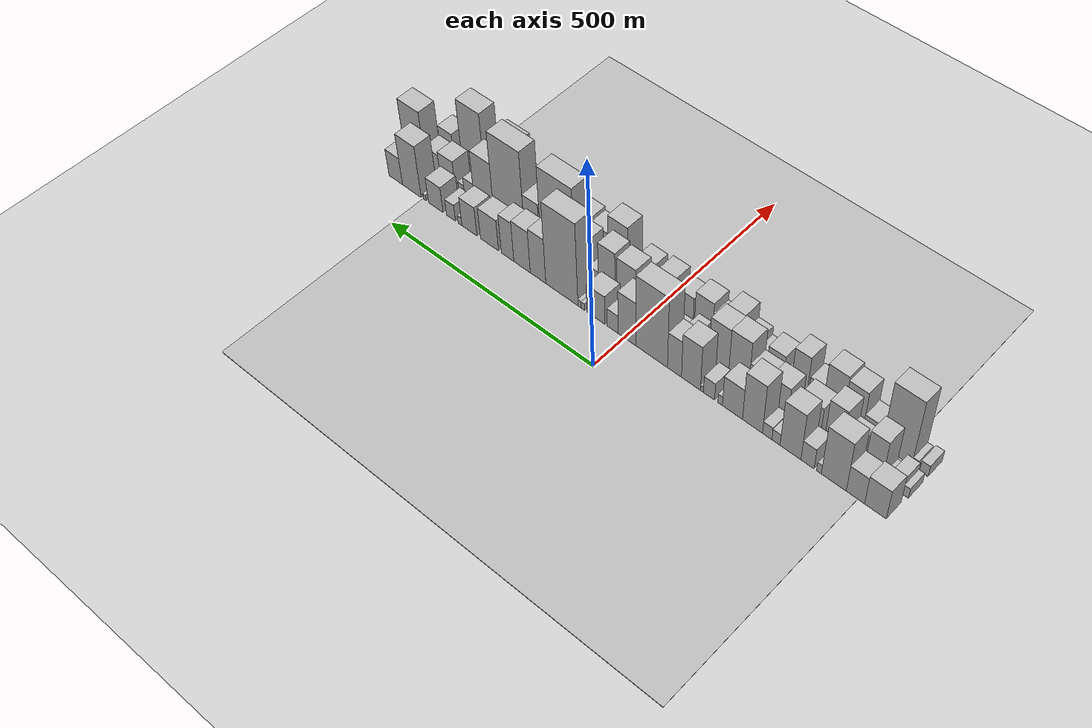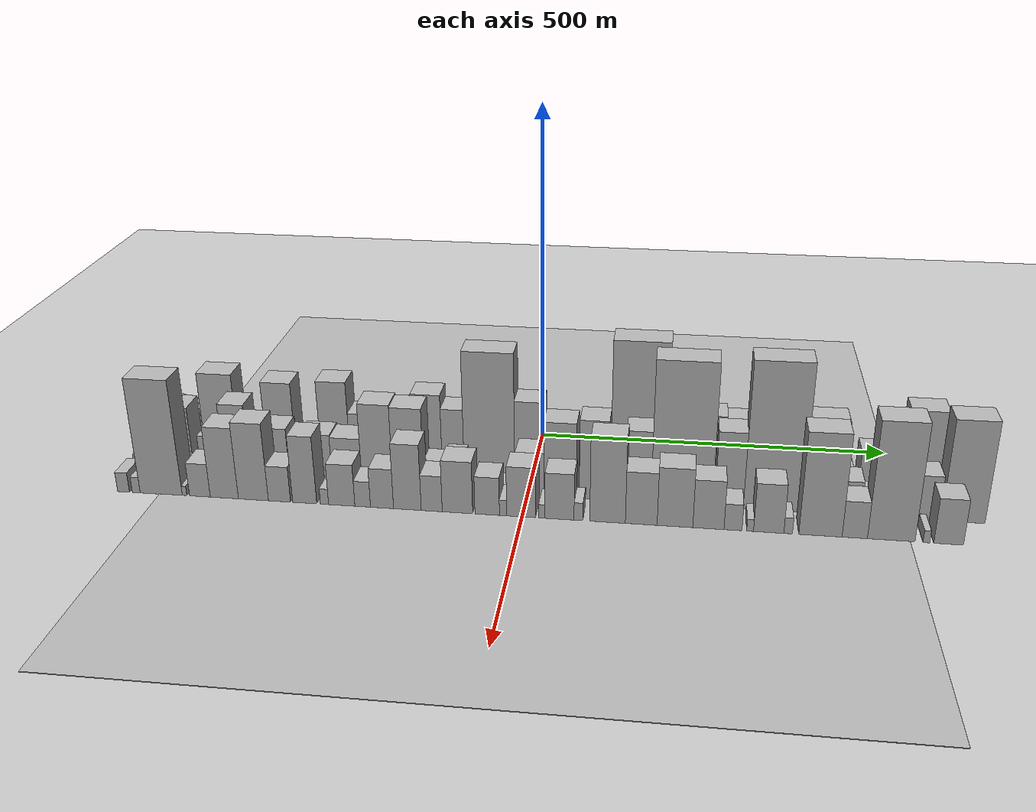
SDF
<?xml version="1.0" encoding="utf-8"?>

<sdf version="1.6">

   <world name="default">

      <gui fullscreen="0">

         <camera name="user_camera">

            <pose>-15 0 4.57585 0 0 0</pose>

            <view_controller>orbit</view_controller>

         </camera>

      </gui>

      <scene>

         <sky>

           <clouds>

             <speed>12</speed>

           </clouds>

         </sky>

         <ambient>0.4 0.4 0.4 1</ambient>

         <background>0.7 0.7 0.7 1</background>

         <shadows>1</shadows>

      </scene>

      <gravity>0 0 -9.8066</gravity>

      <magnetic_field>6e-06 2.3e-05 -4.2e-05</magnetic_field>

      <physics default="0" name="default_physics" type="ode">

         <ode>

            <solver>

               <type>quick</type>

               <iters>10</iters>

               <sor>1.0</sor>

               <use_dynamic_moi_rescaling>0</use_dynamic_moi_rescaling>

            </solver>

            <constraints>

               <cfm>0</cfm>

               <erp>0.2</erp>

               <contact_max_correcting_vel>100</contact_max_correcting_vel>

               <contact_surface_layer>0.001</contact_surface_layer>

            </constraints>

         </ode>

         <max_step_size>0.004</max_step_size>

         <real_time_factor>1</real_time_factor>

         <real_time_update_rate>250</real_time_update_rate>

      </physics>

      <light name="sun" type="directional">

         <cast_shadows>1</cast_shadows>

         <pose>0 0 10 0 0 0</pose>

         <diffuse>0.8 0.8 0.8 1</diffuse>

         <specular>0.2 0.2 0.2 1</specular>

         <attenuation>

            <range>1000</range>

            <constant>0.9</constant>

            <linear>0.01</linear>

            <quadratic>0.001</quadratic>

         </attenuation>

         <direction>-0.5 0.1 -0.9</direction>

      </light>

      <include>

         <name>ground_plane_1</name>

         <uri>model://HANNAS_ground_plane</uri>

         <pose>0 0 0  0 0 0</pose>

      </include>

      <include>

         <name>ground_plane_2</name>

         <uri>model://HANNAS_ground_plane</uri>

         <pose>100 0 0  0 0 0</pose>

      </include>

      <model name="building_1">

         <static>1</static>

         <pose frame="">100.0000 -534.6059 0 0.000000 0.000000 0.000000</pose>

         <link name="link">

            <pose frame="">0 0 39.00 0 0 0</pose>

            <collision name="collision">

               <geometry>

                  <box>

                     <size>40.0000 42.7883 78.0000</size>

                  </box>

               </geometry>

               <max_contacts>10</max_contacts>

               <surface>

                  <contact>

                     <ode/>

                  </contact>

                  <bounce/>

                  <friction>

                     <torsional>

                        <ode/>

                     </torsional>

                     <ode/>

                  </friction>

               </surface>

            </collision>

            <visual name="visual">

               <cast_shadows>0</cast_shadows>

               <geometry>

                  <box>

                     <size>40.0000 42.7883 78.0000</size>

                  </box>

               </geometry>

               <material>

                  <script>

                     <uri>model://HANNAS_wall/materials/scripts</uri>

                     <uri>model://HANNAS_wall/materials/textures</uri>

                     <name>vrc/HANNAS_wall</name>

                  </script>

               </material>

            </visual>

            <self_collide>0</self_collide>

            <enable_wind>0</enable_wind>

            <kinematic>0</kinematic>

         </link>

      </model>

      <model name="building_2">

         <static>1</static>

         <pose frame="">100.0000 -495.0071 0 0.000000 0.000000 0.000000</pose>

         <link name="link">

            <pose frame="">0 0 36.00 0 0 0</pose>

            <collision name="collision">

               <geometry>

                  <box>

                     <size>40.0000 36.4093 72.0000</size>

                  </box>

               </geometry>

               <max_contacts>10</max_contacts>

               <surface>

                  <contact>

                     <ode/>

                  </contact>

                  <bounce/>

                  <friction>

                     <torsional>

                        <ode/>

                     </torsional>

                     <ode/>

                  </friction>

               </surface>

            </collision>

            <visual name="visual">

               <cast_shadows>0</cast_shadows>

               <geometry>

                  <box>

                     <size>40.0000 36.4093 72.0000</size>

                  </box>

               </geometry>

               <material>

                  <script>

                     <uri>model://HANNAS_wall/materials/scripts</uri>

                     <uri>model://HANNAS_wall/materials/textures</uri>

                     <name>vrc/HANNAS_wall</name>

                  </script>

               </material>

            </visual>

            <self_collide>0</self_collide>

            <enable_wind>0</enable_wind>

            <kinematic>0</kinematic>

         </link>

      </model>

      <model name="building_3">

         <static>1</static>

         <pose frame="">100.0000 -451.6534 0 0.000000 0.000000 0.000000</pose>

         <link name="link">

            <pose frame="">0 0 66.00 0 0 0</pose>

            <collision name="collision">

               <geometry>

                  <box>

                     <size>40.0000 50.2981 132.0000</size>

                  </box>

               </geometry>

               <max_contacts>10</max_contacts>

               <surface>

                  <contact>

                     <ode/>

                  </contact>

                  <bounce/>

                  <friction>

                     <torsional>

                        <ode/>

                     </torsional>

                     <ode/>

                  </friction>

               </surface>

            </collision>

            <visual name="visual">

               <cast_shadows>0</cast_shadows>

               <geometry>

                  <box>

                     <size>40.0000 50.2981 132.0000</size>

                  </box>

               </geometry>

               <material>

                  <script>

                     <uri>model://HANNAS_wall/materials/scripts</uri>

                     <uri>model://HANNAS_wall/materials/textures</uri>

                     <name>vrc/HANNAS_wall</name>

                  </script>

               </material>

            </visual>

            <self_collide>0</self_collide>

            <enable_wind>0</enable_wind>

            <kinematic>0</kinematic>

         </link>

      </model>

      <model name="building_4">

         <static>1</static>

         <pose frame="">100.0000 -421.6903 0 0.000000 0.000000 0.000000</pose>

         <link name="link">

            <pose frame="">0 0 12.00 0 0 0</pose>

            <collision name="collision">

               <geometry>

                  <box>

                     <size>40.0000 9.6282 24.0000</size>

                  </box>

               </geometry>

               <max_contacts>10</max_contacts>

               <surface>

                  <contact>

                     <ode/>

                  </contact>

                  <bounce/>

                  <friction>

                     <torsional>

                        <ode/>

                     </torsional>

                     <ode/>

                  </friction>

               </surface>

            </collision>

            <visual name="visual">

               <cast_shadows>0</cast_shadows>

               <geometry>

                  <box>

                     <size>40.0000 9.6282 24.0000</size>

                  </box>

               </geometry>

               <material>

                  <script>

                     <uri>model://HANNAS_wall/materials/scripts</uri>

                     <uri>model://HANNAS_wall/materials/textures</uri>

                     <name>vrc/HANNAS_wall</name>

                  </script>

               </material>

            </visual>

            <self_collide>0</self_collide>

            <enable_wind>0</enable_wind>

            <kinematic>0</kinematic>

         </link>

      </model>

      <model name="building_5">

         <static>1</static>

         <pose frame="">100.0000 -398.3272 0 0.000000 0.000000 0.000000</pose>

         <link name="link">

            <pose frame="">0 0 27.00 0 0 0</pose>

            <collision name="collision">

               <geometry>

                  <box>

                     <size>40.0000 27.0980 54.0000</size>

                  </box>

               </geometry>

               <max_contacts>10</max_contacts>

               <surface>

                  <contact>

                     <ode/>

                  </contact>

                  <bounce/>

                  <friction>

                     <torsional>

                        <ode/>

                     </torsional>

                     <ode/>

                  </friction>

               </surface>

            </collision>

            <visual name="visual">

               <cast_shadows>0</cast_shadows>

               <geometry>

                  <box>

                     <size>40.0000 27.0980 54.0000</size>

                  </box>

               </geometry>

               <material>

                  <script>

                     <uri>model://HANNAS_wall/materials/scripts</uri>

                     <uri>model://HANNAS_wall/materials/textures</uri>

                     <name>vrc/HANNAS_wall</name>

                  </script>

               </material>

            </visual>

            <self_collide>0</self_collide>

            <enable_wind>0</enable_wind>

            <kinematic>0</kinematic>

         </link>

      </model>

      <model name="building_6">

         <static>1</static>

         <pose frame="">100.0000 -363.2109 0 0.000000 0.000000 0.000000</pose>

         <link name="link">

            <pose frame="">0 0 61.50 0 0 0</pose>

            <collision name="collision">

               <geometry>

                  <box>

                     <size>40.0000 43.1346 123.0000</size>

                  </box>

               </geometry>

               <max_contacts>10</max_contacts>

               <surface>

                  <contact>

                     <ode/>

                  </contact>

                  <bounce/>

                  <friction>

                     <torsional>

                        <ode/>

                     </torsional>

                     <ode/>

                  </friction>

               </surface>

            </collision>

            <visual name="visual">

               <cast_shadows>0</cast_shadows>

               <geometry>

                  <box>

                     <size>40.0000 43.1346 123.0000</size>

                  </box>

               </geometry>

               <material>

                  <script>

                     <uri>model://HANNAS_wall/materials/scripts</uri>

                     <uri>model://HANNAS_wall/materials/textures</uri>

                     <name>vrc/HANNAS_wall</name>

                  </script>

               </material>

            </visual>

            <self_collide>0</self_collide>

            <enable_wind>0</enable_wind>

            <kinematic>0</kinematic>

         </link>

      </model>

      <model name="building_7">

         <static>1</static>

         <pose frame="">100.0000 -333.0880 0 0.000000 0.000000 0.000000</pose>

         <link name="link">

            <pose frame="">0 0 15.00 0 0 0</pose>

            <collision name="collision">

               <geometry>

                  <box>

                     <size>40.0000 17.1113 30.0000</size>

                  </box>

               </geometry>

               <max_contacts>10</max_contacts>

               <surface>

                  <contact>

                     <ode/>

                  </contact>

                  <bounce/>

                  <friction>

                     <torsional>

                        <ode/>

                     </torsional>

                     <ode/>

                  </friction>

               </surface>

            </collision>

            <visual name="visual">

               <cast_shadows>0</cast_shadows>

               <geometry>

                  <box>

                     <size>40.0000 17.1113 30.0000</size>

                  </box>

               </geometry>

               <material>

                  <script>

                     <uri>model://HANNAS_wall/materials/scripts</uri>

                     <uri>model://HANNAS_wall/materials/textures</uri>

                     <name>vrc/HANNAS_wall</name>

                  </script>

               </material>

            </visual>

            <self_collide>0</self_collide>

            <enable_wind>0</enable_wind>

            <kinematic>0</kinematic>

         </link>

      </model>

      <model name="building_8">

         <static>1</static>

         <pose frame="">100.0000 -314.6613 0 0.000000 0.000000 0.000000</pose>

         <link name="link">

            <pose frame="">0 0 16.50 0 0 0</pose>

            <collision name="collision">

               <geometry>

                  <box>

                     <size>40.0000 19.7421 33.0000</size>

                  </box>

               </geometry>

               <max_contacts>10</max_contacts>

               <surface>

                  <contact>

                     <ode/>

                  </contact>

                  <bounce/>

                  <friction>

                     <torsional>

                        <ode/>

                     </torsional>

                     <ode/>

                  </friction>

               </surface>

            </collision>

            <visual name="visual">

               <cast_shadows>0</cast_shadows>

               <geometry>

                  <box>

                     <size>40.0000 19.7421 33.0000</size>

                  </box>

               </geometry>

               <material>

                  <script>

                     <uri>model://HANNAS_wall/materials/scripts</uri>

                     <uri>model://HANNAS_wall/materials/textures</uri>

                     <name>vrc/HANNAS_wall</name>

                  </script>

               </material>

            </visual>

            <self_collide>0</self_collide>

            <enable_wind>0</enable_wind>

            <kinematic>0</kinematic>

         </link>

      </model>

      <model name="building_9">

         <static>1</static>

         <pose frame="">100.0000 -283.5166 0 0.000000 0.000000 0.000000</pose>

         <link name="link">

            <pose frame="">0 0 64.50 0 0 0</pose>

            <collision name="collision">

               <geometry>

                  <box>

                     <size>40.0000 42.5474 129.0000</size>

                  </box>

               </geometry>

               <max_contacts>10</max_contacts>

               <surface>

                  <contact>

                     <ode/>

                  </contact>

                  <bounce/>

                  <friction>

                     <torsional>

                        <ode/>

                     </torsional>

                     <ode/>

                  </friction>

               </surface>

            </collision>

            <visual name="visual">

               <cast_shadows>0</cast_shadows>

               <geometry>

                  <box>

                     <size>40.0000 42.5474 129.0000</size>

                  </box>

               </geometry>

               <material>

                  <script>

                     <uri>model://HANNAS_wall/materials/scripts</uri>

                     <uri>model://HANNAS_wall/materials/textures</uri>

                     <name>vrc/HANNAS_wall</name>

                  </script>

               </material>

            </visual>

            <self_collide>0</self_collide>

            <enable_wind>0</enable_wind>

            <kinematic>0</kinematic>

         </link>

      </model>

      <model name="building_10">

         <static>1</static>

         <pose frame="">100.0000 -240.6432 0 0.000000 0.000000 0.000000</pose>

         <link name="link">

            <pose frame="">0 0 40.50 0 0 0</pose>

            <collision name="collision">

               <geometry>

                  <box>

                     <size>40.0000 43.1994 81.0000</size>

                  </box>

               </geometry>

               <max_contacts>10</max_contacts>

               <surface>

                  <contact>

                     <ode/>

                  </contact>

                  <bounce/>

                  <friction>

                     <torsional>

                        <ode/>

                     </torsional>

                     <ode/>

                  </friction>

               </surface>

            </collision>

            <visual name="visual">

               <cast_shadows>0</cast_shadows>

               <geometry>

                  <box>

                     <size>40.0000 43.1994 81.0000</size>

                  </box>

               </geometry>

               <material>

                  <script>

                     <uri>model://HANNAS_wall/materials/scripts</uri>

                     <uri>model://HANNAS_wall/materials/textures</uri>

                     <name>vrc/HANNAS_wall</name>

                  </script>

               </material>

            </visual>

            <self_collide>0</self_collide>

            <enable_wind>0</enable_wind>

            <kinematic>0</kinematic>

         </link>

      </model>

      <model name="building_11">

         <static>1</static>

         <pose frame="">100.0000 -214.1174 0 0.000000 0.000000 0.000000</pose>

         <link name="link">

            <pose frame="">0 0 12.00 0 0 0</pose>

            <collision name="collision">

               <geometry>

                  <box>

                     <size>40.0000 9.8522 24.0000</size>

                  </box>

               </geometry>

               <max_contacts>10</max_contacts>

               <surface>

                  <contact>

                     <ode/>

                  </contact>

                  <bounce/>

                  <friction>

                     <torsional>

                        <ode/>

                     </torsional>

                     <ode/>

                  </friction>

               </surface>

            </collision>

            <visual name="visual">

               <cast_shadows>0</cast_shadows>

               <geometry>

                  <box>

                     <size>40.0000 9.8522 24.0000</size>

                  </box>

               </geometry>

               <material>

                  <script>

                     <uri>model://HANNAS_wall/materials/scripts</uri>

                     <uri>model://HANNAS_wall/materials/textures</uri>

                     <name>vrc/HANNAS_wall</name>

                  </script>

               </material>

            </visual>

            <self_collide>0</self_collide>

            <enable_wind>0</enable_wind>

            <kinematic>0</kinematic>

         </link>

      </model>

      <model name="building_12">

         <static>1</static>

         <pose frame="">100.0000 -189.9528 0 0.000000 0.000000 0.000000</pose>

         <link name="link">

            <pose frame="">0 0 22.50 0 0 0</pose>

            <collision name="collision">

               <geometry>

                  <box>

                     <size>40.0000 24.4770 45.0000</size>

                  </box>

               </geometry>

               <max_contacts>10</max_contacts>

               <surface>

                  <contact>

                     <ode/>

                  </contact>

                  <bounce/>

                  <friction>

                     <torsional>

                        <ode/>

                     </torsional>

                     <ode/>

                  </friction>

               </surface>

            </collision>

            <visual name="visual">

               <cast_shadows>0</cast_shadows>

               <geometry>

                  <box>

                     <size>40.0000 24.4770 45.0000</size>

                  </box>

               </geometry>

               <material>

                  <script>

                     <uri>model://HANNAS_wall/materials/scripts</uri>

                     <uri>model://HANNAS_wall/materials/textures</uri>

                     <name>vrc/HANNAS_wall</name>

                  </script>

               </material>

            </visual>

            <self_collide>0</self_collide>

            <enable_wind>0</enable_wind>

            <kinematic>0</kinematic>

         </link>

      </model>

      <model name="building_13">

         <static>1</static>

         <pose frame="">100.0000 -174.4072 0 0.000000 0.000000 0.000000</pose>

         <link name="link">

            <pose frame="">0 0 7.50 0 0 0</pose>

            <collision name="collision">

               <geometry>

                  <box>

                     <size>40.0000 6.6142 15.0000</size>

                  </box>

               </geometry>

               <max_contacts>10</max_contacts>

               <surface>

                  <contact>

                     <ode/>

                  </contact>

                  <bounce/>

                  <friction>

                     <torsional>

                        <ode/>

                     </torsional>

                     <ode/>

                  </friction>

               </surface>

            </collision>

            <visual name="visual">

               <cast_shadows>0</cast_shadows>

               <geometry>

                  <box>

                     <size>40.0000 6.6142 15.0000</size>

                  </box>

               </geometry>

               <material>

                  <script>

                     <uri>model://HANNAS_wall/materials/scripts</uri>

                     <uri>model://HANNAS_wall/materials/textures</uri>

                     <name>vrc/HANNAS_wall</name>

                  </script>

               </material>

            </visual>

            <self_collide>0</self_collide>

            <enable_wind>0</enable_wind>

            <kinematic>0</kinematic>

         </link>

      </model>

      <model name="building_14">

         <static>1</static>

         <pose frame="">100.0000 -150.1791 0 0.000000 0.000000 0.000000</pose>

         <link name="link">

            <pose frame="">0 0 58.50 0 0 0</pose>

            <collision name="collision">

               <geometry>

                  <box>

                     <size>40.0000 41.8419 117.0000</size>

                  </box>

               </geometry>

               <max_contacts>10</max_contacts>

               <surface>

                  <contact>

                     <ode/>

                  </contact>

                  <bounce/>

                  <friction>

                     <torsional>

                        <ode/>

                     </torsional>

                     <ode/>

                  </friction>

               </surface>

            </collision>

            <visual name="visual">

               <cast_shadows>0</cast_shadows>

               <geometry>

                  <box>

                     <size>40.0000 41.8419 117.0000</size>

                  </box>

               </geometry>

               <material>

                  <script>

                     <uri>model://HANNAS_wall/materials/scripts</uri>

                     <uri>model://HANNAS_wall/materials/textures</uri>

                     <name>vrc/HANNAS_wall</name>

                  </script>

               </material>

            </visual>

            <self_collide>0</self_collide>

            <enable_wind>0</enable_wind>

            <kinematic>0</kinematic>

         </link>

      </model>

      <model name="building_15">

         <static>1</static>

         <pose frame="">100.0000 -113.5795 0 0.000000 0.000000 0.000000</pose>

         <link name="link">

            <pose frame="">0 0 48.00 0 0 0</pose>

            <collision name="collision">

               <geometry>

                  <box>

                     <size>40.0000 31.3573 96.0000</size>

                  </box>

               </geometry>

               <max_contacts>10</max_contacts>

               <surface>

                  <contact>

                     <ode/>

                  </contact>

                  <bounce/>

                  <friction>

                     <torsional>

                        <ode/>

                     </torsional>

                     <ode/>

                  </friction>

               </surface>

            </collision>

            <visual name="visual">

               <cast_shadows>0</cast_shadows>

               <geometry>

                  <box>

                     <size>40.0000 31.3573 96.0000</size>

                  </box>

               </geometry>

               <material>

                  <script>

                     <uri>model://HANNAS_wall/materials/scripts</uri>

                     <uri>model://HANNAS_wall/materials/textures</uri>

                     <name>vrc/HANNAS_wall</name>

                  </script>

               </material>

            </visual>

            <self_collide>0</self_collide>

            <enable_wind>0</enable_wind>

            <kinematic>0</kinematic>

         </link>

      </model>

      <model name="building_16">

         <static>1</static>

         <pose frame="">100.0000 -61.7813 0 0.000000 0.000000 0.000000</pose>

         <link name="link">

            <pose frame="">0 0 93.00 0 0 0</pose>

            <collision name="collision">

               <geometry>

                  <box>

                     <size>40.0000 72.2393 186.0000</size>

                  </box>

               </geometry>

               <max_contacts>10</max_contacts>

               <surface>

                  <contact>

                     <ode/>

                  </contact>

                  <bounce/>

                  <friction>

                     <torsional>

                        <ode/>

                     </torsional>

                     <ode/>

                  </friction>

               </surface>

            </collision>

            <visual name="visual">

               <cast_shadows>0</cast_shadows>

               <geometry>

                  <box>

                     <size>40.0000 72.2393 186.0000</size>

                  </box>

               </geometry>

               <material>

                  <script>

                     <uri>model://HANNAS_wall/materials/scripts</uri>

                     <uri>model://HANNAS_wall/materials/textures</uri>

                     <name>vrc/HANNAS_wall</name>

                  </script>

               </material>

            </visual>

            <self_collide>0</self_collide>

            <enable_wind>0</enable_wind>

            <kinematic>0</kinematic>

         </link>

      </model>

      <model name="building_17">

         <static>1</static>

         <pose frame="">100.0000 -5.4270 0 0.000000 0.000000 0.000000</pose>

         <link name="link">

            <pose frame="">0 0 57.00 0 0 0</pose>

            <collision name="collision">

               <geometry>

                  <box>

                     <size>40.0000 40.4692 114.0000</size>

                  </box>

               </geometry>

               <max_contacts>10</max_contacts>

               <surface>

                  <contact>

                     <ode/>

                  </contact>

                  <bounce/>

                  <friction>

                     <torsional>

                        <ode/>

                     </torsional>

                     <ode/>

                  </friction>

               </surface>

            </collision>

            <visual name="visual">

               <cast_shadows>0</cast_shadows>

               <geometry>

                  <box>

                     <size>40.0000 40.4692 114.0000</size>

                  </box>

               </geometry>

               <material>

                  <script>

                     <uri>model://HANNAS_wall/materials/scripts</uri>

                     <uri>model://HANNAS_wall/materials/textures</uri>

                     <name>vrc/HANNAS_wall</name>

                  </script>

               </material>

            </visual>

            <self_collide>0</self_collide>

            <enable_wind>0</enable_wind>

            <kinematic>0</kinematic>

         </link>

      </model>

      <model name="building_18">

         <static>1</static>

         <pose frame="">100.0000 27.4994 0 0.000000 0.000000 0.000000</pose>

         <link name="link">

            <pose frame="">0 0 24.00 0 0 0</pose>

            <collision name="collision">

               <geometry>

                  <box>

                     <size>40.0000 25.3837 48.0000</size>

                  </box>

               </geometry>

               <max_contacts>10</max_contacts>

               <surface>

                  <contact>

                     <ode/>

                  </contact>

                  <bounce/>

                  <friction>

                     <torsional>

                        <ode/>

                     </torsional>

                     <ode/>

                  </friction>

               </surface>

            </collision>

            <visual name="visual">

               <cast_shadows>0</cast_shadows>

               <geometry>

                  <box>

                     <size>40.0000 25.3837 48.0000</size>

                  </box>

               </geometry>

               <material>

                  <script>

                     <uri>model://HANNAS_wall/materials/scripts</uri>

                     <uri>model://HANNAS_wall/materials/textures</uri>

                     <name>vrc/HANNAS_wall</name>

                  </script>

               </material>

            </visual>

            <self_collide>0</self_collide>

            <enable_wind>0</enable_wind>

            <kinematic>0</kinematic>

         </link>

      </model>

      <model name="building_19">

         <static>1</static>

         <pose frame="">100.0000 66.5059 0 0.000000 0.000000 0.000000</pose>

         <link name="link">

            <pose frame="">0 0 37.50 0 0 0</pose>

            <collision name="collision">

               <geometry>

                  <box>

                     <size>40.0000 42.6294 75.0000</size>

                  </box>

               </geometry>

               <max_contacts>10</max_contacts>

               <surface>

                  <contact>

                     <ode/>

                  </contact>

                  <bounce/>

                  <friction>

                     <torsional>

                        <ode/>

                     </torsional>

                     <ode/>

                  </friction>

               </surface>

            </collision>

            <visual name="visual">

               <cast_shadows>0</cast_shadows>

               <geometry>

                  <box>

                     <size>40.0000 42.6294 75.0000</size>

                  </box>

               </geometry>

               <material>

                  <script>

                     <uri>model://HANNAS_wall/materials/scripts</uri>

                     <uri>model://HANNAS_wall/materials/textures</uri>

                     <name>vrc/HANNAS_wall</name>

                  </script>

               </material>

            </visual>

            <self_collide>0</self_collide>

            <enable_wind>0</enable_wind>

            <kinematic>0</kinematic>

         </link>

      </model>

      <model name="building_20">

         <static>1</static>

         <pose frame="">100.0000 97.0517 0 0.000000 0.000000 0.000000</pose>

         <link name="link">

            <pose frame="">0 0 9.00 0 0 0</pose>

            <collision name="collision">

               <geometry>

                  <box>

                     <size>40.0000 8.4620 18.0000</size>

                  </box>

               </geometry>

               <max_contacts>10</max_contacts>

               <surface>

                  <contact>

                     <ode/>

                  </contact>

                  <bounce/>

                  <friction>

                     <torsional>

                        <ode/>

                     </torsional>

                     <ode/>

                  </friction>

               </surface>

            </collision>

            <visual name="visual">

               <cast_shadows>0</cast_shadows>

               <geometry>

                  <box>

                     <size>40.0000 8.4620 18.0000</size>

                  </box>

               </geometry>

               <material>

                  <script>

                     <uri>model://HANNAS_wall/materials/scripts</uri>

                     <uri>model://HANNAS_wall/materials/textures</uri>

                     <name>vrc/HANNAS_wall</name>

                  </script>

               </material>

            </visual>

            <self_collide>0</self_collide>

            <enable_wind>0</enable_wind>

            <kinematic>0</kinematic>

         </link>

      </model>

      <model name="building_21">

         <static>1</static>

         <pose frame="">100.0000 105.2145 0 0.000000 0.000000 0.000000</pose>

         <link name="link">

            <pose frame="">0 0 9.00 0 0 0</pose>

            <collision name="collision">

               <geometry>

                  <box>

                     <size>40.0000 7.8637 18.0000</size>

                  </box>

               </geometry>

               <max_contacts>10</max_contacts>

               <surface>

                  <contact>

                     <ode/>

                  </contact>

                  <bounce/>

                  <friction>

                     <torsional>

                        <ode/>

                     </torsional>

                     <ode/>

                  </friction>

               </surface>

            </collision>

            <visual name="visual">

               <cast_shadows>0</cast_shadows>

               <geometry>

                  <box>

                     <size>40.0000 7.8637 18.0000</size>

                  </box>

               </geometry>

               <material>

                  <script>

                     <uri>model://HANNAS_wall/materials/scripts</uri>

                     <uri>model://HANNAS_wall/materials/textures</uri>

                     <name>vrc/HANNAS_wall</name>

                  </script>

               </material>

            </visual>

            <self_collide>0</self_collide>

            <enable_wind>0</enable_wind>

            <kinematic>0</kinematic>

         </link>

      </model>

      <model name="building_22">

         <static>1</static>

         <pose frame="">100.0000 147.9191 0 0.000000 0.000000 0.000000</pose>

         <link name="link">

            <pose frame="">0 0 106.50 0 0 0</pose>

            <collision name="collision">

               <geometry>

                  <box>

                     <size>40.0000 77.5454 213.0000</size>

                  </box>

               </geometry>

               <max_contacts>10</max_contacts>

               <surface>

                  <contact>

                     <ode/>

                  </contact>

                  <bounce/>

                  <friction>

                     <torsional>

                        <ode/>

                     </torsional>

                     <ode/>

                  </friction>

               </surface>

            </collision>

            <visual name="visual">

               <cast_shadows>0</cast_shadows>

               <geometry>

                  <box>

                     <size>40.0000 77.5454 213.0000</size>

                  </box>

               </geometry>

               <material>

                  <script>

                     <uri>model://HANNAS_wall/materials/scripts</uri>

                     <uri>model://HANNAS_wall/materials/textures</uri>

                     <name>vrc/HANNAS_wall</name>

                  </script>

               </material>

            </visual>

            <self_collide>0</self_collide>

            <enable_wind>0</enable_wind>

            <kinematic>0</kinematic>

         </link>

      </model>

      <model name="building_23">

         <static>1</static>

         <pose frame="">100.0000 205.8057 0 0.000000 0.000000 0.000000</pose>

         <link name="link">

            <pose frame="">0 0 58.50 0 0 0</pose>

            <collision name="collision">

               <geometry>

                  <box>

                     <size>40.0000 38.2280 117.0000</size>

                  </box>

               </geometry>

               <max_contacts>10</max_contacts>

               <surface>

                  <contact>

                     <ode/>

                  </contact>

                  <bounce/>

                  <friction>

                     <torsional>

                        <ode/>

                     </torsional>

                     <ode/>

                  </friction>

               </surface>

            </collision>

            <visual name="visual">

               <cast_shadows>0</cast_shadows>

               <geometry>

                  <box>

                     <size>40.0000 38.2280 117.0000</size>

                  </box>

               </geometry>

               <material>

                  <script>

                     <uri>model://HANNAS_wall/materials/scripts</uri>

                     <uri>model://HANNAS_wall/materials/textures</uri>

                     <name>vrc/HANNAS_wall</name>

                  </script>

               </material>

            </visual>

            <self_collide>0</self_collide>

            <enable_wind>0</enable_wind>

            <kinematic>0</kinematic>

         </link>

      </model>

      <model name="building_24">

         <static>1</static>

         <pose frame="">100.0000 245.2790 0 0.000000 0.000000 0.000000</pose>

         <link name="link">

            <pose frame="">0 0 54.00 0 0 0</pose>

            <collision name="collision">

               <geometry>

                  <box>

                     <size>40.0000 40.7185 108.0000</size>

                  </box>

               </geometry>

               <max_contacts>10</max_contacts>

               <surface>

                  <contact>

                     <ode/>

                  </contact>

                  <bounce/>

                  <friction>

                     <torsional>

                        <ode/>

                     </torsional>

                     <ode/>

                  </friction>

               </surface>

            </collision>

            <visual name="visual">

               <cast_shadows>0</cast_shadows>

               <geometry>

                  <box>

                     <size>40.0000 40.7185 108.0000</size>

                  </box>

               </geometry>

               <material>

                  <script>

                     <uri>model://HANNAS_wall/materials/scripts</uri>

                     <uri>model://HANNAS_wall/materials/textures</uri>

                     <name>vrc/HANNAS_wall</name>

                  </script>

               </material>

            </visual>

            <self_collide>0</self_collide>

            <enable_wind>0</enable_wind>

            <kinematic>0</kinematic>

         </link>

      </model>

      <model name="building_25">

         <static>1</static>

         <pose frame="">100.0000 281.2911 0 0.000000 0.000000 0.000000</pose>

         <link name="link">

            <pose frame="">0 0 51.00 0 0 0</pose>

            <collision name="collision">

               <geometry>

                  <box>

                     <size>40.0000 31.3057 102.0000</size>

                  </box>

               </geometry>

               <max_contacts>10</max_contacts>

               <surface>

                  <contact>

                     <ode/>

                  </contact>

                  <bounce/>

                  <friction>

                     <torsional>

                        <ode/>

                     </torsional>

                     <ode/>

                  </friction>

               </surface>

            </collision>

            <visual name="visual">

               <cast_shadows>0</cast_shadows>

               <geometry>

                  <box>

                     <size>40.0000 31.3057 102.0000</size>

                  </box>

               </geometry>

               <material>

                  <script>

                     <uri>model://HANNAS_wall/materials/scripts</uri>

                     <uri>model://HANNAS_wall/materials/textures</uri>

                     <name>vrc/HANNAS_wall</name>

                  </script>

               </material>

            </visual>

            <self_collide>0</self_collide>

            <enable_wind>0</enable_wind>

            <kinematic>0</kinematic>

         </link>

      </model>

      <model name="building_26">

         <static>1</static>

         <pose frame="">100.0000 326.9286 0 0.000000 0.000000 0.000000</pose>

         <link name="link">

            <pose frame="">0 0 40.50 0 0 0</pose>

            <collision name="collision">

               <geometry>

                  <box>

                     <size>40.0000 45.9691 81.0000</size>

                  </box>

               </geometry>

               <max_contacts>10</max_contacts>

               <surface>

                  <contact>

                     <ode/>

                  </contact>

                  <bounce/>

                  <friction>

                     <torsional>

                        <ode/>

                     </torsional>

                     <ode/>

                  </friction>

               </surface>

            </collision>

            <visual name="visual">

               <cast_shadows>0</cast_shadows>

               <geometry>

                  <box>

                     <size>40.0000 45.9691 81.0000</size>

                  </box>

               </geometry>

               <material>

                  <script>

                     <uri>model://HANNAS_wall/materials/scripts</uri>

                     <uri>model://HANNAS_wall/materials/textures</uri>

                     <name>vrc/HANNAS_wall</name>

                  </script>

               </material>

            </visual>

            <self_collide>0</self_collide>

            <enable_wind>0</enable_wind>

            <kinematic>0</kinematic>

         </link>

      </model>

      <model name="building_27">

         <static>1</static>

         <pose frame="">100.0000 378.2967 0 0.000000 0.000000 0.000000</pose>

         <link name="link">

            <pose frame="">0 0 37.50 0 0 0</pose>

            <collision name="collision">

               <geometry>

                  <box>

                     <size>40.0000 38.7671 75.0000</size>

                  </box>

               </geometry>

               <max_contacts>10</max_contacts>

               <surface>

                  <contact>

                     <ode/>

                  </contact>

                  <bounce/>

                  <friction>

                     <torsional>

                        <ode/>

                     </torsional>

                     <ode/>

                  </friction>

               </surface>

            </collision>

            <visual name="visual">

               <cast_shadows>0</cast_shadows>

               <geometry>

                  <box>

                     <size>40.0000 38.7671 75.0000</size>

                  </box>

               </geometry>

               <material>

                  <script>

                     <uri>model://HANNAS_wall/materials/scripts</uri>

                     <uri>model://HANNAS_wall/materials/textures</uri>

                     <name>vrc/HANNAS_wall</name>

                  </script>

               </material>

            </visual>

            <self_collide>0</self_collide>

            <enable_wind>0</enable_wind>

            <kinematic>0</kinematic>

         </link>

      </model>

      <model name="building_28">

         <static>1</static>

         <pose frame="">100.0000 402.6422 0 0.000000 0.000000 0.000000</pose>

         <link name="link">

            <pose frame="">0 0 10.50 0 0 0</pose>

            <collision name="collision">

               <geometry>

                  <box>

                     <size>40.0000 9.9240 21.0000</size>

                  </box>

               </geometry>

               <max_contacts>10</max_contacts>

               <surface>

                  <contact>

                     <ode/>

                  </contact>

                  <bounce/>

                  <friction>

                     <torsional>

                        <ode/>

                     </torsional>

                     <ode/>

                  </friction>

               </surface>

            </collision>

            <visual name="visual">

               <cast_shadows>0</cast_shadows>

               <geometry>

                  <box>

                     <size>40.0000 9.9240 21.0000</size>

                  </box>

               </geometry>

               <material>

                  <script>

                     <uri>model://HANNAS_wall/materials/scripts</uri>

                     <uri>model://HANNAS_wall/materials/textures</uri>

                     <name>vrc/HANNAS_wall</name>

                  </script>

               </material>

            </visual>

            <self_collide>0</self_collide>

            <enable_wind>0</enable_wind>

            <kinematic>0</kinematic>

         </link>

      </model>

      <model name="building_29">

         <static>1</static>

         <pose frame="">100.0000 426.2392 0 0.000000 0.000000 0.000000</pose>

         <link name="link">

            <pose frame="">0 0 21.00 0 0 0</pose>

            <collision name="collision">

               <geometry>

                  <box>

                     <size>40.0000 23.2699 42.0000</size>

                  </box>

               </geometry>

               <max_contacts>10</max_contacts>

               <surface>

                  <contact>

                     <ode/>

                  </contact>

                  <bounce/>

                  <friction>

                     <torsional>

                        <ode/>

                     </torsional>

                     <ode/>

                  </friction>

               </surface>

            </collision>

            <visual name="visual">

               <cast_shadows>0</cast_shadows>

               <geometry>

                  <box>

                     <size>40.0000 23.2699 42.0000</size>

                  </box>

               </geometry>

               <material>

                  <script>

                     <uri>model://HANNAS_wall/materials/scripts</uri>

                     <uri>model://HANNAS_wall/materials/textures</uri>

                     <name>vrc/HANNAS_wall</name>

                  </script>

               </material>

            </visual>

            <self_collide>0</self_collide>

            <enable_wind>0</enable_wind>

            <kinematic>0</kinematic>

         </link>

      </model>

      <model name="building_30">

         <static>1</static>

         <pose frame="">100.0000 466.0563 0 0.000000 0.000000 0.000000</pose>

         <link name="link">

            <pose frame="">0 0 33.00 0 0 0</pose>

            <collision name="collision">

               <geometry>

                  <box>

                     <size>40.0000 38.3643 66.0000</size>

                  </box>

               </geometry>

               <max_contacts>10</max_contacts>

               <surface>

                  <contact>

                     <ode/>

                  </contact>

                  <bounce/>

                  <friction>

                     <torsional>

                        <ode/>

                     </torsional>

                     <ode/>

                  </friction>

               </surface>

            </collision>

            <visual name="visual">

               <cast_shadows>0</cast_shadows>

               <geometry>

                  <box>

                     <size>40.0000 38.3643 66.0000</size>

                  </box>

               </geometry>

               <material>

                  <script>

                     <uri>model://HANNAS_wall/materials/scripts</uri>

                     <uri>model://HANNAS_wall/materials/textures</uri>

                     <name>vrc/HANNAS_wall</name>

                  </script>

               </material>

            </visual>

            <self_collide>0</self_collide>

            <enable_wind>0</enable_wind>

            <kinematic>0</kinematic>

         </link>

      </model>

      <model name="building_31">

         <static>1</static>

         <pose frame="">100.0000 494.9782 0 0.000000 0.000000 0.000000</pose>

         <link name="link">

            <pose frame="">0 0 7.50 0 0 0</pose>

            <collision name="collision">

               <geometry>

                  <box>

                     <size>40.0000 7.4796 15.0000</size>

                  </box>

               </geometry>

               <max_contacts>10</max_contacts>

               <surface>

                  <contact>

                     <ode/>

                  </contact>

                  <bounce/>

                  <friction>

                     <torsional>

                        <ode/>

                     </torsional>

                     <ode/>

                  </friction>

               </surface>

            </collision>

            <visual name="visual">

               <cast_shadows>0</cast_shadows>

               <geometry>

                  <box>

                     <size>40.0000 7.4796 15.0000</size>

                  </box>

               </geometry>

               <material>

                  <script>

                     <uri>model://HANNAS_wall/materials/scripts</uri>

                     <uri>model://HANNAS_wall/materials/textures</uri>

                     <name>vrc/HANNAS_wall</name>

                  </script>

               </material>

            </visual>

            <self_collide>0</self_collide>

            <enable_wind>0</enable_wind>

            <kinematic>0</kinematic>

         </link>

      </model>

      <model name="building_32">

         <static>1</static>

         <pose frame="">100.0000 529.8098 0 0.000000 0.000000 0.000000</pose>

         <link name="link">

            <pose frame="">0 0 66.00 0 0 0</pose>

            <collision name="collision">

               <geometry>

                  <box>

                     <size>40.0000 50.1836 132.0000</size>

                  </box>

               </geometry>

               <max_contacts>10</max_contacts>

               <surface>

                  <contact>

                     <ode/>

                  </contact>

                  <bounce/>

                  <friction>

                     <torsional>

                        <ode/>

                     </torsional>

                     <ode/>

                  </friction>

               </surface>

            </collision>

            <visual name="visual">

               <cast_shadows>0</cast_shadows>

               <geometry>

                  <box>

                     <size>40.0000 50.1836 132.0000</size>

                  </box>

               </geometry>

               <material>

                  <script>

                     <uri>model://HANNAS_wall/materials/scripts</uri>

                     <uri>model://HANNAS_wall/materials/textures</uri>

                     <name>vrc/HANNAS_wall</name>

                  </script>

               </material>

            </visual>

            <self_collide>0</self_collide>

            <enable_wind>0</enable_wind>

            <kinematic>0</kinematic>

         </link>

      </model>

      <model name="building_33">

         <static>1</static>

         <pose frame="">100.0000 573.1475 0 0.000000 0.000000 0.000000</pose>

         <link name="link">

            <pose frame="">0 0 34.50 0 0 0</pose>

            <collision name="collision">

               <geometry>

                  <box>

                     <size>40.0000 36.4918 69.0000</size>

                  </box>

               </geometry>

               <max_contacts>10</max_contacts>

               <surface>

                  <contact>

                     <ode/>

                  </contact>

                  <bounce/>

                  <friction>

                     <torsional>

                        <ode/>

                     </torsional>

                     <ode/>

                  </friction>

               </surface>

            </collision>

            <visual name="visual">

               <cast_shadows>0</cast_shadows>

               <geometry>

                  <box>

                     <size>40.0000 36.4918 69.0000</size>

                  </box>

               </geometry>

               <material>

                  <script>

                     <uri>model://HANNAS_wall/materials/scripts</uri>

                     <uri>model://HANNAS_wall/materials/textures</uri>

                     <name>vrc/HANNAS_wall</name>

                  </script>

               </material>

            </visual>

            <self_collide>0</self_collide>

            <enable_wind>0</enable_wind>

            <kinematic>0</kinematic>

         </link>

      </model>

      <model name="building_34">

         <static>1</static>

         <pose frame="">155.0000 -554.1464 0 0.000000 0.000000 0.000000</pose>

         <link name="link">

            <pose frame="">0 0 13.50 0 0 0</pose>

            <collision name="collision">

               <geometry>

                  <box>

                     <size>40.0000 11.7072 27.0000</size>

                  </box>

               </geometry>

               <max_contacts>10</max_contacts>

               <surface>

                  <contact>

                     <ode/>

                  </contact>

                  <bounce/>

                  <friction>

                     <torsional>

                        <ode/>

                     </torsional>

                     <ode/>

                  </friction>

               </surface>

            </collision>

            <visual name="visual">

               <cast_shadows>0</cast_shadows>

               <geometry>

                  <box>

                     <size>40.0000 11.7072 27.0000</size>

                  </box>

               </geometry>

               <material>

                  <script>

                     <uri>model://HANNAS_wall/materials/scripts</uri>

                     <uri>model://HANNAS_wall/materials/textures</uri>

                     <name>vrc/HANNAS_wall</name>

                  </script>

               </material>

            </visual>

            <self_collide>0</self_collide>

            <enable_wind>0</enable_wind>

            <kinematic>0</kinematic>

         </link>

      </model>

      <model name="building_35">

         <static>1</static>

         <pose frame="">155.0000 -535.8460 0 0.000000 0.000000 0.000000</pose>

         <link name="link">

            <pose frame="">0 0 22.50 0 0 0</pose>

            <collision name="collision">

               <geometry>

                  <box>

                     <size>40.0000 24.8936 45.0000</size>

                  </box>

               </geometry>

               <max_contacts>10</max_contacts>

               <surface>

                  <contact>

                     <ode/>

                  </contact>

                  <bounce/>

                  <friction>

                     <torsional>

                        <ode/>

                     </torsional>

                     <ode/>

                  </friction>

               </surface>

            </collision>

            <visual name="visual">

               <cast_shadows>0</cast_shadows>

               <geometry>

                  <box>

                     <size>40.0000 24.8936 45.0000</size>

                  </box>

               </geometry>

               <material>

                  <script>

                     <uri>model://HANNAS_wall/materials/scripts</uri>

                     <uri>model://HANNAS_wall/materials/textures</uri>

                     <name>vrc/HANNAS_wall</name>

                  </script>

               </material>

            </visual>

            <self_collide>0</self_collide>

            <enable_wind>0</enable_wind>

            <kinematic>0</kinematic>

         </link>

      </model>

      <model name="building_36">

         <static>1</static>

         <pose frame="">155.0000 -520.1779 0 0.000000 0.000000 0.000000</pose>

         <link name="link">

            <pose frame="">0 0 7.50 0 0 0</pose>

            <collision name="collision">

               <geometry>

                  <box>

                     <size>40.0000 6.4425 15.0000</size>

                  </box>

               </geometry>

               <max_contacts>10</max_contacts>

               <surface>

                  <contact>

                     <ode/>

                  </contact>

                  <bounce/>

                  <friction>

                     <torsional>

                        <ode/>

                     </torsional>

                     <ode/>

                  </friction>

               </surface>

            </collision>

            <visual name="visual">

               <cast_shadows>0</cast_shadows>

               <geometry>

                  <box>

                     <size>40.0000 6.4425 15.0000</size>

                  </box>

               </geometry>

               <material>

                  <script>

                     <uri>model://HANNAS_wall/materials/scripts</uri>

                     <uri>model://HANNAS_wall/materials/textures</uri>

                     <name>vrc/HANNAS_wall</name>

                  </script>

               </material>

            </visual>

            <self_collide>0</self_collide>

            <enable_wind>0</enable_wind>

            <kinematic>0</kinematic>

         </link>

      </model>

      <model name="building_37">

         <static>1</static>

         <pose frame="">155.0000 -512.6137 0 0.000000 0.000000 0.000000</pose>

         <link name="link">

            <pose frame="">0 0 9.00 0 0 0</pose>

            <collision name="collision">

               <geometry>

                  <box>

                     <size>40.0000 8.6860 18.0000</size>

                  </box>

               </geometry>

               <max_contacts>10</max_contacts>

               <surface>

                  <contact>

                     <ode/>

                  </contact>

                  <bounce/>

                  <friction>

                     <torsional>

                        <ode/>

                     </torsional>

                     <ode/>

                  </friction>

               </surface>

            </collision>

            <visual name="visual">

               <cast_shadows>0</cast_shadows>

               <geometry>

                  <box>

                     <size>40.0000 8.6860 18.0000</size>

                  </box>

               </geometry>

               <material>

                  <script>

                     <uri>model://HANNAS_wall/materials/scripts</uri>

                     <uri>model://HANNAS_wall/materials/textures</uri>

                     <name>vrc/HANNAS_wall</name>

                  </script>

               </material>

            </visual>

            <self_collide>0</self_collide>

            <enable_wind>0</enable_wind>

            <kinematic>0</kinematic>

         </link>

      </model>

      <model name="building_38">

         <static>1</static>

         <pose frame="">155.0000 -490.0451 0 0.000000 0.000000 0.000000</pose>

         <link name="link">

            <pose frame="">0 0 52.50 0 0 0</pose>

            <collision name="collision">

               <geometry>

                  <box>

                     <size>40.0000 36.4512 105.0000</size>

                  </box>

               </geometry>

               <max_contacts>10</max_contacts>

               <surface>

                  <contact>

                     <ode/>

                  </contact>

                  <bounce/>

                  <friction>

                     <torsional>

                        <ode/>

                     </torsional>

                     <ode/>

                  </friction>

               </surface>

            </collision>

            <visual name="visual">

               <cast_shadows>0</cast_shadows>

               <geometry>

                  <box>

                     <size>40.0000 36.4512 105.0000</size>

                  </box>

               </geometry>

               <material>

                  <script>

                     <uri>model://HANNAS_wall/materials/scripts</uri>

                     <uri>model://HANNAS_wall/materials/textures</uri>

                     <name>vrc/HANNAS_wall</name>

                  </script>

               </material>

            </visual>

            <self_collide>0</self_collide>

            <enable_wind>0</enable_wind>

            <kinematic>0</kinematic>

         </link>

      </model>

      <model name="building_39">

         <static>1</static>

         <pose frame="">155.0000 -444.6192 0 0.000000 0.000000 0.000000</pose>

         <link name="link">

            <pose frame="">0 0 31.50 0 0 0</pose>

            <collision name="collision">

               <geometry>

                  <box>

                     <size>40.0000 34.4006 63.0000</size>

                  </box>

               </geometry>

               <max_contacts>10</max_contacts>

               <surface>

                  <contact>

                     <ode/>

                  </contact>

                  <bounce/>

                  <friction>

                     <torsional>

                        <ode/>

                     </torsional>

                     <ode/>

                  </friction>

               </surface>

            </collision>

            <visual name="visual">

               <cast_shadows>0</cast_shadows>

               <geometry>

                  <box>

                     <size>40.0000 34.4006 63.0000</size>

                  </box>

               </geometry>

               <material>

                  <script>

                     <uri>model://HANNAS_wall/materials/scripts</uri>

                     <uri>model://HANNAS_wall/materials/textures</uri>

                     <name>vrc/HANNAS_wall</name>

                  </script>

               </material>

            </visual>

            <self_collide>0</self_collide>

            <enable_wind>0</enable_wind>

            <kinematic>0</kinematic>

         </link>

      </model>

      <model name="building_40">

         <static>1</static>

         <pose frame="">155.0000 -409.1548 0 0.000000 0.000000 0.000000</pose>

         <link name="link">

            <pose frame="">0 0 57.00 0 0 0</pose>

            <collision name="collision">

               <geometry>

                  <box>

                     <size>40.0000 36.5283 114.0000</size>

                  </box>

               </geometry>

               <max_contacts>10</max_contacts>

               <surface>

                  <contact>

                     <ode/>

                  </contact>

                  <bounce/>

                  <friction>

                     <torsional>

                        <ode/>

                     </torsional>

                     <ode/>

                  </friction>

               </surface>

            </collision>

            <visual name="visual">

               <cast_shadows>0</cast_shadows>

               <geometry>

                  <box>

                     <size>40.0000 36.5283 114.0000</size>

                  </box>

               </geometry>

               <material>

                  <script>

                     <uri>model://HANNAS_wall/materials/scripts</uri>

                     <uri>model://HANNAS_wall/materials/textures</uri>

                     <name>vrc/HANNAS_wall</name>

                  </script>

               </material>

            </visual>

            <self_collide>0</self_collide>

            <enable_wind>0</enable_wind>

            <kinematic>0</kinematic>

         </link>

      </model>

      <model name="building_41">

         <static>1</static>

         <pose frame="">155.0000 -357.8791 0 0.000000 0.000000 0.000000</pose>

         <link name="link">

            <pose frame="">0 0 40.50 0 0 0</pose>

            <collision name="collision">

               <geometry>

                  <box>

                     <size>40.0000 48.0231 81.0000</size>

                  </box>

               </geometry>

               <max_contacts>10</max_contacts>

               <surface>

                  <contact>

                     <ode/>

                  </contact>

                  <bounce/>

                  <friction>

                     <torsional>

                        <ode/>

                     </torsional>

                     <ode/>

                  </friction>

               </surface>

            </collision>

            <visual name="visual">

               <cast_shadows>0</cast_shadows>

               <geometry>

                  <box>

                     <size>40.0000 48.0231 81.0000</size>

                  </box>

               </geometry>

               <material>

                  <script>

                     <uri>model://HANNAS_wall/materials/scripts</uri>

                     <uri>model://HANNAS_wall/materials/textures</uri>

                     <name>vrc/HANNAS_wall</name>

                  </script>

               </material>

            </visual>

            <self_collide>0</self_collide>

            <enable_wind>0</enable_wind>

            <kinematic>0</kinematic>

         </link>

      </model>

      <model name="building_42">

         <static>1</static>

         <pose frame="">155.0000 -324.7988 0 0.000000 0.000000 0.000000</pose>

         <link name="link">

            <pose frame="">0 0 18.00 0 0 0</pose>

            <collision name="collision">

               <geometry>

                  <box>

                     <size>40.0000 18.1375 36.0000</size>

                  </box>

               </geometry>

               <max_contacts>10</max_contacts>

               <surface>

                  <contact>

                     <ode/>

                  </contact>

                  <bounce/>

                  <friction>

                     <torsional>

                        <ode/>

                     </torsional>

                     <ode/>

                  </friction>

               </surface>

            </collision>

            <visual name="visual">

               <cast_shadows>0</cast_shadows>

               <geometry>

                  <box>

                     <size>40.0000 18.1375 36.0000</size>

                  </box>

               </geometry>

               <material>

                  <script>

                     <uri>model://HANNAS_wall/materials/scripts</uri>

                     <uri>model://HANNAS_wall/materials/textures</uri>

                     <name>vrc/HANNAS_wall</name>

                  </script>

               </material>

            </visual>

            <self_collide>0</self_collide>

            <enable_wind>0</enable_wind>

            <kinematic>0</kinematic>

         </link>

      </model>

      <model name="building_43">

         <static>1</static>

         <pose frame="">155.0000 -294.3853 0 0.000000 0.000000 0.000000</pose>

         <link name="link">

            <pose frame="">0 0 37.50 0 0 0</pose>

            <collision name="collision">

               <geometry>

                  <box>

                     <size>40.0000 42.6894 75.0000</size>

                  </box>

               </geometry>

               <max_contacts>10</max_contacts>

               <surface>

                  <contact>

                     <ode/>

                  </contact>

                  <bounce/>

                  <friction>

                     <torsional>

                        <ode/>

                     </torsional>

                     <ode/>

                  </friction>

               </surface>

            </collision>

            <visual name="visual">

               <cast_shadows>0</cast_shadows>

               <geometry>

                  <box>

                     <size>40.0000 42.6894 75.0000</size>

                  </box>

               </geometry>

               <material>

                  <script>

                     <uri>model://HANNAS_wall/materials/scripts</uri>

                     <uri>model://HANNAS_wall/materials/textures</uri>

                     <name>vrc/HANNAS_wall</name>

                  </script>

               </material>

            </visual>

            <self_collide>0</self_collide>

            <enable_wind>0</enable_wind>

            <kinematic>0</kinematic>

         </link>

      </model>

      <model name="building_44">

         <static>1</static>

         <pose frame="">155.0000 -252.0402 0 0.000000 0.000000 0.000000</pose>

         <link name="link">

            <pose frame="">0 0 36.00 0 0 0</pose>

            <collision name="collision">

               <geometry>

                  <box>

                     <size>40.0000 42.0008 72.0000</size>

                  </box>

               </geometry>

               <max_contacts>10</max_contacts>

               <surface>

                  <contact>

                     <ode/>

                  </contact>

                  <bounce/>

                  <friction>

                     <torsional>

                        <ode/>

                     </torsional>

                     <ode/>

                  </friction>

               </surface>

            </collision>

            <visual name="visual">

               <cast_shadows>0</cast_shadows>

               <geometry>

                  <box>

                     <size>40.0000 42.0008 72.0000</size>

                  </box>

               </geometry>

               <material>

                  <script>

                     <uri>model://HANNAS_wall/materials/scripts</uri>

                     <uri>model://HANNAS_wall/materials/textures</uri>

                     <name>vrc/HANNAS_wall</name>

                  </script>

               </material>

            </visual>

            <self_collide>0</self_collide>

            <enable_wind>0</enable_wind>

            <kinematic>0</kinematic>

         </link>

      </model>

      <model name="building_45">

         <static>1</static>

         <pose frame="">155.0000 -209.2373 0 0.000000 0.000000 0.000000</pose>

         <link name="link">

            <pose frame="">0 0 63.00 0 0 0</pose>

            <collision name="collision">

               <geometry>

                  <box>

                     <size>40.0000 43.6050 126.0000</size>

                  </box>

               </geometry>

               <max_contacts>10</max_contacts>

               <surface>

                  <contact>

                     <ode/>

                  </contact>

                  <bounce/>

                  <friction>

                     <torsional>

                        <ode/>

                     </torsional>

                     <ode/>

                  </friction>

               </surface>

            </collision>

            <visual name="visual">

               <cast_shadows>0</cast_shadows>

               <geometry>

                  <box>

                     <size>40.0000 43.6050 126.0000</size>

                  </box>

               </geometry>

               <material>

                  <script>

                     <uri>model://HANNAS_wall/materials/scripts</uri>

                     <uri>model://HANNAS_wall/materials/textures</uri>

                     <name>vrc/HANNAS_wall</name>

                  </script>

               </material>

            </visual>

            <self_collide>0</self_collide>

            <enable_wind>0</enable_wind>

            <kinematic>0</kinematic>

         </link>

      </model>

      <model name="building_46">

         <static>1</static>

         <pose frame="">155.0000 -165.6142 0 0.000000 0.000000 0.000000</pose>

         <link name="link">

            <pose frame="">0 0 61.50 0 0 0</pose>

            <collision name="collision">

               <geometry>

                  <box>

                     <size>40.0000 43.6411 123.0000</size>

                  </box>

               </geometry>

               <max_contacts>10</max_contacts>

               <surface>

                  <contact>

                     <ode/>

                  </contact>

                  <bounce/>

                  <friction>

                     <torsional>

                        <ode/>

                     </torsional>

                     <ode/>

                  </friction>

               </surface>

            </collision>

            <visual name="visual">

               <cast_shadows>0</cast_shadows>

               <geometry>

                  <box>

                     <size>40.0000 43.6411 123.0000</size>

                  </box>

               </geometry>

               <material>

                  <script>

                     <uri>model://HANNAS_wall/materials/scripts</uri>

                     <uri>model://HANNAS_wall/materials/textures</uri>

                     <name>vrc/HANNAS_wall</name>

                  </script>

               </material>

            </visual>

            <self_collide>0</self_collide>

            <enable_wind>0</enable_wind>

            <kinematic>0</kinematic>

         </link>

      </model>

      <model name="building_47">

         <static>1</static>

         <pose frame="">155.0000 -131.7472 0 0.000000 0.000000 0.000000</pose>

         <link name="link">

            <pose frame="">0 0 21.00 0 0 0</pose>

            <collision name="collision">

               <geometry>

                  <box>

                     <size>40.0000 24.0929 42.0000</size>

                  </box>

               </geometry>

               <max_contacts>10</max_contacts>

               <surface>

                  <contact>

                     <ode/>

                  </contact>

                  <bounce/>

                  <friction>

                     <torsional>

                        <ode/>

                     </torsional>

                     <ode/>

                  </friction>

               </surface>

            </collision>

            <visual name="visual">

               <cast_shadows>0</cast_shadows>

               <geometry>

                  <box>

                     <size>40.0000 24.0929 42.0000</size>

                  </box>

               </geometry>

               <material>

                  <script>

                     <uri>model://HANNAS_wall/materials/scripts</uri>

                     <uri>model://HANNAS_wall/materials/textures</uri>

                     <name>vrc/HANNAS_wall</name>

                  </script>

               </material>

            </visual>

            <self_collide>0</self_collide>

            <enable_wind>0</enable_wind>

            <kinematic>0</kinematic>

         </link>

      </model>

      <model name="building_48">

         <static>1</static>

         <pose frame="">155.0000 -101.8067 0 0.000000 0.000000 0.000000</pose>

         <link name="link">

            <pose frame="">0 0 25.50 0 0 0</pose>

            <collision name="collision">

               <geometry>

                  <box>

                     <size>40.0000 27.7881 51.0000</size>

                  </box>

               </geometry>

               <max_contacts>10</max_contacts>

               <surface>

                  <contact>

                     <ode/>

                  </contact>

                  <bounce/>

                  <friction>

                     <torsional>

                        <ode/>

                     </torsional>

                     <ode/>

                  </friction>

               </surface>

            </collision>

            <visual name="visual">

               <cast_shadows>0</cast_shadows>

               <geometry>

                  <box>

                     <size>40.0000 27.7881 51.0000</size>

                  </box>

               </geometry>

               <material>

                  <script>

                     <uri>model://HANNAS_wall/materials/scripts</uri>

                     <uri>model://HANNAS_wall/materials/textures</uri>

                     <name>vrc/HANNAS_wall</name>

                  </script>

               </material>

            </visual>

            <self_collide>0</self_collide>

            <enable_wind>0</enable_wind>

            <kinematic>0</kinematic>

         </link>

      </model>

      <model name="building_49">

         <static>1</static>

         <pose frame="">155.0000 2.4951 0 0.000000 0.000000 0.000000</pose>

         <link name="link">

            <pose frame="">0 0 33.00 0 0 0</pose>

            <collision name="collision">

               <geometry>

                  <box>

                     <size>40.0000 38.9385 66.0000</size>

                  </box>

               </geometry>

               <max_contacts>10</max_contacts>

               <surface>

                  <contact>

                     <ode/>

                  </contact>

                  <bounce/>

                  <friction>

                     <torsional>

                        <ode/>

                     </torsional>

                     <ode/>

                  </friction>

               </surface>

            </collision>

            <visual name="visual">

               <cast_shadows>0</cast_shadows>

               <geometry>

                  <box>

                     <size>40.0000 38.9385 66.0000</size>

                  </box>

               </geometry>

               <material>

                  <script>

                     <uri>model://HANNAS_wall/materials/scripts</uri>

                     <uri>model://HANNAS_wall/materials/textures</uri>

                     <name>vrc/HANNAS_wall</name>

                  </script>

               </material>

            </visual>

            <self_collide>0</self_collide>

            <enable_wind>0</enable_wind>

            <kinematic>0</kinematic>

         </link>

      </model>

      <model name="building_50">

         <static>1</static>

         <pose frame="">155.0000 44.1461 0 0.000000 0.000000 0.000000</pose>

         <link name="link">

            <pose frame="">0 0 57.00 0 0 0</pose>

            <collision name="collision">

               <geometry>

                  <box>

                     <size>40.0000 44.3635 114.0000</size>

                  </box>

               </geometry>

               <max_contacts>10</max_contacts>

               <surface>

                  <contact>

                     <ode/>

                  </contact>

                  <bounce/>

                  <friction>

                     <torsional>

                        <ode/>

                     </torsional>

                     <ode/>

                  </friction>

               </surface>

            </collision>

            <visual name="visual">

               <cast_shadows>0</cast_shadows>

               <geometry>

                  <box>

                     <size>40.0000 44.3635 114.0000</size>

                  </box>

               </geometry>

               <material>

                  <script>

                     <uri>model://HANNAS_wall/materials/scripts</uri>

                     <uri>model://HANNAS_wall/materials/textures</uri>

                     <name>vrc/HANNAS_wall</name>

                  </script>

               </material>

            </visual>

            <self_collide>0</self_collide>

            <enable_wind>0</enable_wind>

            <kinematic>0</kinematic>

         </link>

      </model>

      <model name="building_51">

         <static>1</static>

         <pose frame="">155.0000 90.1031 0 0.000000 0.000000 0.000000</pose>

         <link name="link">

            <pose frame="">0 0 60.00 0 0 0</pose>

            <collision name="collision">

               <geometry>

                  <box>

                     <size>40.0000 39.5505 120.0000</size>

                  </box>

               </geometry>

               <max_contacts>10</max_contacts>

               <surface>

                  <contact>

                     <ode/>

                  </contact>

                  <bounce/>

                  <friction>

                     <torsional>

                        <ode/>

                     </torsional>

                     <ode/>

                  </friction>

               </surface>

            </collision>

            <visual name="visual">

               <cast_shadows>0</cast_shadows>

               <geometry>

                  <box>

                     <size>40.0000 39.5505 120.0000</size>

                  </box>

               </geometry>

               <material>

                  <script>

                     <uri>model://HANNAS_wall/materials/scripts</uri>

                     <uri>model://HANNAS_wall/materials/textures</uri>

                     <name>vrc/HANNAS_wall</name>

                  </script>

               </material>

            </visual>

            <self_collide>0</self_collide>

            <enable_wind>0</enable_wind>

            <kinematic>0</kinematic>

         </link>

      </model>

      <model name="building_52">

         <static>1</static>

         <pose frame="">155.0000 121.1536 0 0.000000 0.000000 0.000000</pose>

         <link name="link">

            <pose frame="">0 0 21.00 0 0 0</pose>

            <collision name="collision">

               <geometry>

                  <box>

                     <size>40.0000 22.5504 42.0000</size>

                  </box>

               </geometry>

               <max_contacts>10</max_contacts>

               <surface>

                  <contact>

                     <ode/>

                  </contact>

                  <bounce/>

                  <friction>

                     <torsional>

                        <ode/>

                     </torsional>

                     <ode/>

                  </friction>

               </surface>

            </collision>

            <visual name="visual">

               <cast_shadows>0</cast_shadows>

               <geometry>

                  <box>

                     <size>40.0000 22.5504 42.0000</size>

                  </box>

               </geometry>

               <material>

                  <script>

                     <uri>model://HANNAS_wall/materials/scripts</uri>

                     <uri>model://HANNAS_wall/materials/textures</uri>

                     <name>vrc/HANNAS_wall</name>

                  </script>

               </material>

            </visual>

            <self_collide>0</self_collide>

            <enable_wind>0</enable_wind>

            <kinematic>0</kinematic>

         </link>

      </model>

      <model name="building_53">

         <static>1</static>

         <pose frame="">155.0000 149.9112 0 0.000000 0.000000 0.000000</pose>

         <link name="link">

            <pose frame="">0 0 54.00 0 0 0</pose>

            <collision name="collision">

               <geometry>

                  <box>

                     <size>40.0000 34.9647 108.0000</size>

                  </box>

               </geometry>

               <max_contacts>10</max_contacts>

               <surface>

                  <contact>

                     <ode/>

                  </contact>

                  <bounce/>

                  <friction>

                     <torsional>

                        <ode/>

                     </torsional>

                     <ode/>

                  </friction>

               </surface>

            </collision>

            <visual name="visual">

               <cast_shadows>0</cast_shadows>

               <geometry>

                  <box>

                     <size>40.0000 34.9647 108.0000</size>

                  </box>

               </geometry>

               <material>

                  <script>

                     <uri>model://HANNAS_wall/materials/scripts</uri>

                     <uri>model://HANNAS_wall/materials/textures</uri>

                     <name>vrc/HANNAS_wall</name>

                  </script>

               </material>

            </visual>

            <self_collide>0</self_collide>

            <enable_wind>0</enable_wind>

            <kinematic>0</kinematic>

         </link>

      </model>

      <model name="building_54">

         <static>1</static>

         <pose frame="">155.0000 208.5201 0 0.000000 0.000000 0.000000</pose>

         <link name="link">

            <pose frame="">0 0 106.50 0 0 0</pose>

            <collision name="collision">

               <geometry>

                  <box>

                     <size>40.0000 82.2531 213.0000</size>

                  </box>

               </geometry>

               <max_contacts>10</max_contacts>

               <surface>

                  <contact>

                     <ode/>

                  </contact>

                  <bounce/>

                  <friction>

                     <torsional>

                        <ode/>

                     </torsional>

                     <ode/>

                  </friction>

               </surface>

            </collision>

            <visual name="visual">

               <cast_shadows>0</cast_shadows>

               <geometry>

                  <box>

                     <size>40.0000 82.2531 213.0000</size>

                  </box>

               </geometry>

               <material>

                  <script>

                     <uri>model://HANNAS_wall/materials/scripts</uri>

                     <uri>model://HANNAS_wall/materials/textures</uri>

                     <name>vrc/HANNAS_wall</name>

                  </script>

               </material>

            </visual>

            <self_collide>0</self_collide>

            <enable_wind>0</enable_wind>

            <kinematic>0</kinematic>

         </link>

      </model>

      <model name="building_55">

         <static>1</static>

         <pose frame="">155.0000 271.6360 0 0.000000 0.000000 0.000000</pose>

         <link name="link">

            <pose frame="">0 0 57.00 0 0 0</pose>

            <collision name="collision">

               <geometry>

                  <box>

                     <size>40.0000 37.9787 114.0000</size>

                  </box>

               </geometry>

               <max_contacts>10</max_contacts>

               <surface>

                  <contact>

                     <ode/>

                  </contact>

                  <bounce/>

                  <friction>

                     <torsional>

                        <ode/>

                     </torsional>

                     <ode/>

                  </friction>

               </surface>

            </collision>

            <visual name="visual">

               <cast_shadows>0</cast_shadows>

               <geometry>

                  <box>

                     <size>40.0000 37.9787 114.0000</size>

                  </box>

               </geometry>

               <material>

                  <script>

                     <uri>model://HANNAS_wall/materials/scripts</uri>

                     <uri>model://HANNAS_wall/materials/textures</uri>

                     <name>vrc/HANNAS_wall</name>

                  </script>

               </material>

            </visual>

            <self_collide>0</self_collide>

            <enable_wind>0</enable_wind>

            <kinematic>0</kinematic>

         </link>

      </model>

      <model name="building_56">

         <static>1</static>

         <pose frame="">155.0000 329.6477 0 0.000000 0.000000 0.000000</pose>

         <link name="link">

            <pose frame="">0 0 109.50 0 0 0</pose>

            <collision name="collision">

               <geometry>

                  <box>

                     <size>40.0000 78.0448 219.0000</size>

                  </box>

               </geometry>

               <max_contacts>10</max_contacts>

               <surface>

                  <contact>

                     <ode/>

                  </contact>

                  <bounce/>

                  <friction>

                     <torsional>

                        <ode/>

                     </torsional>

                     <ode/>

                  </friction>

               </surface>

            </collision>

            <visual name="visual">

               <cast_shadows>0</cast_shadows>

               <geometry>

                  <box>

                     <size>40.0000 78.0448 219.0000</size>

                  </box>

               </geometry>

               <material>

                  <script>

                     <uri>model://HANNAS_wall/materials/scripts</uri>

                     <uri>model://HANNAS_wall/materials/textures</uri>

                     <name>vrc/HANNAS_wall</name>

                  </script>

               </material>

            </visual>

            <self_collide>0</self_collide>

            <enable_wind>0</enable_wind>

            <kinematic>0</kinematic>

         </link>

      </model>

      <model name="building_57">

         <static>1</static>

         <pose frame="">155.0000 393.9776 0 0.000000 0.000000 0.000000</pose>

         <link name="link">

            <pose frame="">0 0 69.00 0 0 0</pose>

            <collision name="collision">

               <geometry>

                  <box>

                     <size>40.0000 50.6150 138.0000</size>

                  </box>

               </geometry>

               <max_contacts>10</max_contacts>

               <surface>

                  <contact>

                     <ode/>

                  </contact>

                  <bounce/>

                  <friction>

                     <torsional>

                        <ode/>

                     </torsional>

                     <ode/>

                  </friction>

               </surface>

            </collision>

            <visual name="visual">

               <cast_shadows>0</cast_shadows>

               <geometry>

                  <box>

                     <size>40.0000 50.6150 138.0000</size>

                  </box>

               </geometry>

               <material>

                  <script>

                     <uri>model://HANNAS_wall/materials/scripts</uri>

                     <uri>model://HANNAS_wall/materials/textures</uri>

                     <name>vrc/HANNAS_wall</name>

                  </script>

               </material>

            </visual>

            <self_collide>0</self_collide>

            <enable_wind>0</enable_wind>

            <kinematic>0</kinematic>

         </link>

      </model>

      <model name="building_58">

         <static>1</static>

         <pose frame="">155.0000 432.3639 0 0.000000 0.000000 0.000000</pose>

         <link name="link">

            <pose frame="">0 0 25.50 0 0 0</pose>

            <collision name="collision">

               <geometry>

                  <box>

                     <size>40.0000 26.1575 51.0000</size>

                  </box>

               </geometry>

               <max_contacts>10</max_contacts>

               <surface>

                  <contact>

                     <ode/>

                  </contact>

                  <bounce/>

                  <friction>

                     <torsional>

                        <ode/>

                     </torsional>

                     <ode/>

                  </friction>

               </surface>

            </collision>

            <visual name="visual">

               <cast_shadows>0</cast_shadows>

               <geometry>

                  <box>

                     <size>40.0000 26.1575 51.0000</size>

                  </box>

               </geometry>

               <material>

                  <script>

                     <uri>model://HANNAS_wall/materials/scripts</uri>

                     <uri>model://HANNAS_wall/materials/textures</uri>

                     <name>vrc/HANNAS_wall</name>

                  </script>

               </material>

            </visual>

            <self_collide>0</self_collide>

            <enable_wind>0</enable_wind>

            <kinematic>0</kinematic>

         </link>

      </model>

      <model name="building_59">

         <static>1</static>

         <pose frame="">155.0000 452.9784 0 0.000000 0.000000 0.000000</pose>

         <link name="link">

            <pose frame="">0 0 15.00 0 0 0</pose>

            <collision name="collision">

               <geometry>

                  <box>

                     <size>40.0000 15.0715 30.0000</size>

                  </box>

               </geometry>

               <max_contacts>10</max_contacts>

               <surface>

                  <contact>

                     <ode/>

                  </contact>

                  <bounce/>

                  <friction>

                     <torsional>

                        <ode/>

                     </torsional>

                     <ode/>

                  </friction>

               </surface>

            </collision>

            <visual name="visual">

               <cast_shadows>0</cast_shadows>

               <geometry>

                  <box>

                     <size>40.0000 15.0715 30.0000</size>

                  </box>

               </geometry>

               <material>

                  <script>

                     <uri>model://HANNAS_wall/materials/scripts</uri>

                     <uri>model://HANNAS_wall/materials/textures</uri>

                     <name>vrc/HANNAS_wall</name>

                  </script>

               </material>

            </visual>

            <self_collide>0</self_collide>

            <enable_wind>0</enable_wind>

            <kinematic>0</kinematic>

         </link>

      </model>

      <model name="building_60">

         <static>1</static>

         <pose frame="">155.0000 489.3522 0 0.000000 0.000000 0.000000</pose>

         <link name="link">

            <pose frame="">0 0 37.50 0 0 0</pose>

            <collision name="collision">

               <geometry>

                  <box>

                     <size>40.0000 39.6760 75.0000</size>

                  </box>

               </geometry>

               <max_contacts>10</max_contacts>

               <surface>

                  <contact>

                     <ode/>

                  </contact>

                  <bounce/>

                  <friction>

                     <torsional>

                        <ode/>

                     </torsional>

                     <ode/>

                  </friction>

               </surface>

            </collision>

            <visual name="visual">

               <cast_shadows>0</cast_shadows>

               <geometry>

                  <box>

                     <size>40.0000 39.6760 75.0000</size>

                  </box>

               </geometry>

               <material>

                  <script>

                     <uri>model://HANNAS_wall/materials/scripts</uri>

                     <uri>model://HANNAS_wall/materials/textures</uri>

                     <name>vrc/HANNAS_wall</name>

                  </script>

               </material>

            </visual>

            <self_collide>0</self_collide>

            <enable_wind>0</enable_wind>

            <kinematic>0</kinematic>

         </link>

      </model>

      <model name="building_61">

         <static>1</static>

         <pose frame="">155.0000 527.2222 0 0.000000 0.000000 0.000000</pose>

         <link name="link">

            <pose frame="">0 0 33.00 0 0 0</pose>

            <collision name="collision">

               <geometry>

                  <box>

                     <size>40.0000 36.0640 66.0000</size>

                  </box>

               </geometry>

               <max_contacts>10</max_contacts>

               <surface>

                  <contact>

                     <ode/>

                  </contact>

                  <bounce/>

                  <friction>

                     <torsional>

                        <ode/>

                     </torsional>

                     <ode/>

                  </friction>

               </surface>

            </collision>

            <visual name="visual">

               <cast_shadows>0</cast_shadows>

               <geometry>

                  <box>

                     <size>40.0000 36.0640 66.0000</size>

                  </box>

               </geometry>

               <material>

                  <script>

                     <uri>model://HANNAS_wall/materials/scripts</uri>

                     <uri>model://HANNAS_wall/materials/textures</uri>

                     <name>vrc/HANNAS_wall</name>

                  </script>

               </material>

            </visual>

            <self_collide>0</self_collide>

            <enable_wind>0</enable_wind>

            <kinematic>0</kinematic>

         </link>

      </model>

      <model name="building_62">

         <static>1</static>

         <pose frame="">155.0000 576.1279 0 0.000000 0.000000 0.000000</pose>

         <link name="link">

            <pose frame="">0 0 75.00 0 0 0</pose>

            <collision name="collision">

               <geometry>

                  <box>

                     <size>40.0000 55.7476 150.0000</size>

                  </box>

               </geometry>

               <max_contacts>10</max_contacts>

               <surface>

                  <contact>

                     <ode/>

                  </contact>

                  <bounce/>

                  <friction>

                     <torsional>

                        <ode/>

                     </torsional>

                     <ode/>

                  </friction>

               </surface>

            </collision>

            <visual name="visual">

               <cast_shadows>0</cast_shadows>

               <geometry>

                  <box>

                     <size>40.0000 55.7476 150.0000</size>

                  </box>

               </geometry>

               <material>

                  <script>

                     <uri>model://HANNAS_wall/materials/scripts</uri>

                     <uri>model://HANNAS_wall/materials/textures</uri>

                     <name>vrc/HANNAS_wall</name>

                  </script>

               </material>

            </visual>

            <self_collide>0</self_collide>

            <enable_wind>0</enable_wind>

            <kinematic>0</kinematic>

         </link>

      </model>

      <model name="building_63">

         <static>1</static>

         <pose frame="">210.0000 -551.4670 0 0.000000 0.000000 0.000000</pose>

         <link name="link">

            <pose frame="">0 0 15.00 0 0 0</pose>

            <collision name="collision">

               <geometry>

                  <box>

                     <size>40.0000 17.0660 30.0000</size>

                  </box>

               </geometry>

               <max_contacts>10</max_contacts>

               <surface>

                  <contact>

                     <ode/>

                  </contact>

                  <bounce/>

                  <friction>

                     <torsional>

                        <ode/>

                     </torsional>

                     <ode/>

                  </friction>

               </surface>

            </collision>

            <visual name="visual">

               <cast_shadows>0</cast_shadows>

               <geometry>

                  <box>

                     <size>40.0000 17.0660 30.0000</size>

                  </box>

               </geometry>

               <material>

                  <script>

                     <uri>model://HANNAS_wall/materials/scripts</uri>

                     <uri>model://HANNAS_wall/materials/textures</uri>

                     <name>vrc/HANNAS_wall</name>

                  </script>

               </material>

            </visual>

            <self_collide>0</self_collide>

            <enable_wind>0</enable_wind>

            <kinematic>0</kinematic>

         </link>

      </model>

      <model name="building_64">

         <static>1</static>

         <pose frame="">210.0000 -533.3005 0 0.000000 0.000000 0.000000</pose>

         <link name="link">

            <pose frame="">0 0 12.00 0 0 0</pose>

            <collision name="collision">

               <geometry>

                  <box>

                     <size>40.0000 11.2670 24.0000</size>

                  </box>

               </geometry>

               <max_contacts>10</max_contacts>

               <surface>

                  <contact>

                     <ode/>

                  </contact>

                  <bounce/>

                  <friction>

                     <torsional>

                        <ode/>

                     </torsional>

                     <ode/>

                  </friction>

               </surface>

            </collision>

            <visual name="visual">

               <cast_shadows>0</cast_shadows>

               <geometry>

                  <box>

                     <size>40.0000 11.2670 24.0000</size>

                  </box>

               </geometry>

               <material>

                  <script>

                     <uri>model://HANNAS_wall/materials/scripts</uri>

                     <uri>model://HANNAS_wall/materials/textures</uri>

                     <name>vrc/HANNAS_wall</name>

                  </script>

               </material>

            </visual>

            <self_collide>0</self_collide>

            <enable_wind>0</enable_wind>

            <kinematic>0</kinematic>

         </link>

      </model>

      <model name="building_65">

         <static>1</static>

         <pose frame="">210.0000 -497.6394 0 0.000000 0.000000 0.000000</pose>

         <link name="link">

            <pose frame="">0 0 87.00 0 0 0</pose>

            <collision name="collision">

               <geometry>

                  <box>

                     <size>40.0000 60.0551 174.0000</size>

                  </box>

               </geometry>

               <max_contacts>10</max_contacts>

               <surface>

                  <contact>

                     <ode/>

                  </contact>

                  <bounce/>

                  <friction>

                     <torsional>

                        <ode/>

                     </torsional>

                     <ode/>

                  </friction>

               </surface>

            </collision>

            <visual name="visual">

               <cast_shadows>0</cast_shadows>

               <geometry>

                  <box>

                     <size>40.0000 60.0551 174.0000</size>

                  </box>

               </geometry>

               <material>

                  <script>

                     <uri>model://HANNAS_wall/materials/scripts</uri>

                     <uri>model://HANNAS_wall/materials/textures</uri>

                     <name>vrc/HANNAS_wall</name>

                  </script>

               </material>

            </visual>

            <self_collide>0</self_collide>

            <enable_wind>0</enable_wind>

            <kinematic>0</kinematic>

         </link>

      </model>

      <model name="building_66">

         <static>1</static>

         <pose frame="">210.0000 -464.4536 0 0.000000 0.000000 0.000000</pose>

         <link name="link">

            <pose frame="">0 0 7.50 0 0 0</pose>

            <collision name="collision">

               <geometry>

                  <box>

                     <size>40.0000 6.3166 15.0000</size>

                  </box>

               </geometry>

               <max_contacts>10</max_contacts>

               <surface>

                  <contact>

                     <ode/>

                  </contact>

                  <bounce/>

                  <friction>

                     <torsional>

                        <ode/>

                     </torsional>

                     <ode/>

                  </friction>

               </surface>

            </collision>

            <visual name="visual">

               <cast_shadows>0</cast_shadows>

               <geometry>

                  <box>

                     <size>40.0000 6.3166 15.0000</size>

                  </box>

               </geometry>

               <material>

                  <script>

                     <uri>model://HANNAS_wall/materials/scripts</uri>

                     <uri>model://HANNAS_wall/materials/textures</uri>

                     <name>vrc/HANNAS_wall</name>

                  </script>

               </material>

            </visual>

            <self_collide>0</self_collide>

            <enable_wind>0</enable_wind>

            <kinematic>0</kinematic>

         </link>

      </model>

      <model name="building_67">

         <static>1</static>

         <pose frame="">210.0000 -442.6400 0 0.000000 0.000000 0.000000</pose>

         <link name="link">

            <pose frame="">0 0 25.50 0 0 0</pose>

            <collision name="collision">

               <geometry>

                  <box>

                     <size>40.0000 29.3106 51.0000</size>

                  </box>

               </geometry>

               <max_contacts>10</max_contacts>

               <surface>

                  <contact>

                     <ode/>

                  </contact>

                  <bounce/>

                  <friction>

                     <torsional>

                        <ode/>

                     </torsional>

                     <ode/>

                  </friction>

               </surface>

            </collision>

            <visual name="visual">

               <cast_shadows>0</cast_shadows>

               <geometry>

                  <box>

                     <size>40.0000 29.3106 51.0000</size>

                  </box>

               </geometry>

               <material>

                  <script>

                     <uri>model://HANNAS_wall/materials/scripts</uri>

                     <uri>model://HANNAS_wall/materials/textures</uri>

                     <name>vrc/HANNAS_wall</name>

                  </script>

               </material>

            </visual>

            <self_collide>0</self_collide>

            <enable_wind>0</enable_wind>

            <kinematic>0</kinematic>

         </link>

      </model>

      <model name="building_68">

         <static>1</static>

         <pose frame="">210.0000 -408.2236 0 0.000000 0.000000 0.000000</pose>

         <link name="link">

            <pose frame="">0 0 54.00 0 0 0</pose>

            <collision name="collision">

               <geometry>

                  <box>

                     <size>40.0000 39.5223 108.0000</size>

                  </box>

               </geometry>

               <max_contacts>10</max_contacts>

               <surface>

                  <contact>

                     <ode/>

                  </contact>

                  <bounce/>

                  <friction>

                     <torsional>

                        <ode/>

                     </torsional>

                     <ode/>

                  </friction>

               </surface>

            </collision>

            <visual name="visual">

               <cast_shadows>0</cast_shadows>

               <geometry>

                  <box>

                     <size>40.0000 39.5223 108.0000</size>

                  </box>

               </geometry>

               <material>

                  <script>

                     <uri>model://HANNAS_wall/materials/scripts</uri>

                     <uri>model://HANNAS_wall/materials/textures</uri>

                     <name>vrc/HANNAS_wall</name>

                  </script>

               </material>

            </visual>

            <self_collide>0</self_collide>

            <enable_wind>0</enable_wind>

            <kinematic>0</kinematic>

         </link>

      </model>

      <model name="building_69">

         <static>1</static>

         <pose frame="">210.0000 -367.4800 0 0.000000 0.000000 0.000000</pose>

         <link name="link">

            <pose frame="">0 0 58.50 0 0 0</pose>

            <collision name="collision">

               <geometry>

                  <box>

                     <size>40.0000 41.9648 117.0000</size>

                  </box>

               </geometry>

               <max_contacts>10</max_contacts>

               <surface>

                  <contact>

                     <ode/>

                  </contact>

                  <bounce/>

                  <friction>

                     <torsional>

                        <ode/>

                     </torsional>

                     <ode/>

                  </friction>

               </surface>

            </collision>

            <visual name="visual">

               <cast_shadows>0</cast_shadows>

               <geometry>

                  <box>

                     <size>40.0000 41.9648 117.0000</size>

                  </box>

               </geometry>

               <material>

                  <script>

                     <uri>model://HANNAS_wall/materials/scripts</uri>

                     <uri>model://HANNAS_wall/materials/textures</uri>

                     <name>vrc/HANNAS_wall</name>

                  </script>

               </material>

            </visual>

            <self_collide>0</self_collide>

            <enable_wind>0</enable_wind>

            <kinematic>0</kinematic>

         </link>

      </model>

      <model name="building_70">

         <static>1</static>

         <pose frame="">210.0000 -331.0093 0 0.000000 0.000000 0.000000</pose>

         <link name="link">

            <pose frame="">0 0 27.00 0 0 0</pose>

            <collision name="collision">

               <geometry>

                  <box>

                     <size>40.0000 30.9766 54.0000</size>

                  </box>

               </geometry>

               <max_contacts>10</max_contacts>

               <surface>

                  <contact>

                     <ode/>

                  </contact>

                  <bounce/>

                  <friction>

                     <torsional>

                        <ode/>

                     </torsional>

                     <ode/>

                  </friction>

               </surface>

            </collision>

            <visual name="visual">

               <cast_shadows>0</cast_shadows>

               <geometry>

                  <box>

                     <size>40.0000 30.9766 54.0000</size>

                  </box>

               </geometry>

               <material>

                  <script>

                     <uri>model://HANNAS_wall/materials/scripts</uri>

                     <uri>model://HANNAS_wall/materials/textures</uri>

                     <name>vrc/HANNAS_wall</name>

                  </script>

               </material>

            </visual>

            <self_collide>0</self_collide>

            <enable_wind>0</enable_wind>

            <kinematic>0</kinematic>

         </link>

      </model>

      <model name="building_71">

         <static>1</static>

         <pose frame="">210.0000 -295.8694 0 0.000000 0.000000 0.000000</pose>

         <link name="link">

            <pose frame="">0 0 51.00 0 0 0</pose>

            <collision name="collision">

               <geometry>

                  <box>

                     <size>40.0000 33.3031 102.0000</size>

                  </box>

               </geometry>

               <max_contacts>10</max_contacts>

               <surface>

                  <contact>

                     <ode/>

                  </contact>

                  <bounce/>

                  <friction>

                     <torsional>

                        <ode/>

                     </torsional>

                     <ode/>

                  </friction>

               </surface>

            </collision>

            <visual name="visual">

               <cast_shadows>0</cast_shadows>

               <geometry>

                  <box>

                     <size>40.0000 33.3031 102.0000</size>

                  </box>

               </geometry>

               <material>

                  <script>

                     <uri>model://HANNAS_wall/materials/scripts</uri>

                     <uri>model://HANNAS_wall/materials/textures</uri>

                     <name>vrc/HANNAS_wall</name>

                  </script>

               </material>

            </visual>

            <self_collide>0</self_collide>

            <enable_wind>0</enable_wind>

            <kinematic>0</kinematic>

         </link>

      </model>

      <model name="building_72">

         <static>1</static>

         <pose frame="">210.0000 -268.5393 0 0.000000 0.000000 0.000000</pose>

         <link name="link">

            <pose frame="">0 0 12.00 0 0 0</pose>

            <collision name="collision">

               <geometry>

                  <box>

                     <size>40.0000 11.3571 24.0000</size>

                  </box>

               </geometry>

               <max_contacts>10</max_contacts>

               <surface>

                  <contact>

                     <ode/>

                  </contact>

                  <bounce/>

                  <friction>

                     <torsional>

                        <ode/>

                     </torsional>

                     <ode/>

                  </friction>

               </surface>

            </collision>

            <visual name="visual">

               <cast_shadows>0</cast_shadows>

               <geometry>

                  <box>

                     <size>40.0000 11.3571 24.0000</size>

                  </box>

               </geometry>

               <material>

                  <script>

                     <uri>model://HANNAS_wall/materials/scripts</uri>

                     <uri>model://HANNAS_wall/materials/textures</uri>

                     <name>vrc/HANNAS_wall</name>

                  </script>

               </material>

            </visual>

            <self_collide>0</self_collide>

            <enable_wind>0</enable_wind>

            <kinematic>0</kinematic>

         </link>

      </model>

      <model name="building_73">

         <static>1</static>

         <pose frame="">210.0000 -244.7300 0 0.000000 0.000000 0.000000</pose>

         <link name="link">

            <pose frame="">0 0 31.50 0 0 0</pose>

            <collision name="collision">

               <geometry>

                  <box>

                     <size>40.0000 36.2616 63.0000</size>

                  </box>

               </geometry>

               <max_contacts>10</max_contacts>

               <surface>

                  <contact>

                     <ode/>

                  </contact>

                  <bounce/>

                  <friction>

                     <torsional>

                        <ode/>

                     </torsional>

                     <ode/>

                  </friction>

               </surface>

            </collision>

            <visual name="visual">

               <cast_shadows>0</cast_shadows>

               <geometry>

                  <box>

                     <size>40.0000 36.2616 63.0000</size>

                  </box>

               </geometry>

               <material>

                  <script>

                     <uri>model://HANNAS_wall/materials/scripts</uri>

                     <uri>model://HANNAS_wall/materials/textures</uri>

                     <name>vrc/HANNAS_wall</name>

                  </script>

               </material>

            </visual>

            <self_collide>0</self_collide>

            <enable_wind>0</enable_wind>

            <kinematic>0</kinematic>

         </link>

      </model>

      <model name="building_74">

         <static>1</static>

         <pose frame="">210.0000 -215.9005 0 0.000000 0.000000 0.000000</pose>

         <link name="link">

            <pose frame="">0 0 19.50 0 0 0</pose>

            <collision name="collision">

               <geometry>

                  <box>

                     <size>40.0000 21.3973 39.0000</size>

                  </box>

               </geometry>

               <max_contacts>10</max_contacts>

               <surface>

                  <contact>

                     <ode/>

                  </contact>

                  <bounce/>

                  <friction>

                     <torsional>

                        <ode/>

                     </torsional>

                     <ode/>

                  </friction>

               </surface>

            </collision>

            <visual name="visual">

               <cast_shadows>0</cast_shadows>

               <geometry>

                  <box>

                     <size>40.0000 21.3973 39.0000</size>

                  </box>

               </geometry>

               <material>

                  <script>

                     <uri>model://HANNAS_wall/materials/scripts</uri>

                     <uri>model://HANNAS_wall/materials/textures</uri>

                     <name>vrc/HANNAS_wall</name>

                  </script>

               </material>

            </visual>

            <self_collide>0</self_collide>

            <enable_wind>0</enable_wind>

            <kinematic>0</kinematic>

         </link>

      </model>

      <model name="building_75">

         <static>1</static>

         <pose frame="">210.0000 -189.4502 0 0.000000 0.000000 0.000000</pose>

         <link name="link">

            <pose frame="">0 0 30.00 0 0 0</pose>

            <collision name="collision">

               <geometry>

                  <box>

                     <size>40.0000 31.5033 60.0000</size>

                  </box>

               </geometry>

               <max_contacts>10</max_contacts>

               <surface>

                  <contact>

                     <ode/>

                  </contact>

                  <bounce/>

                  <friction>

                     <torsional>

                        <ode/>

                     </torsional>

                     <ode/>

                  </friction>

               </surface>

            </collision>

            <visual name="visual">

               <cast_shadows>0</cast_shadows>

               <geometry>

                  <box>

                     <size>40.0000 31.5033 60.0000</size>

                  </box>

               </geometry>

               <material>

                  <script>

                     <uri>model://HANNAS_wall/materials/scripts</uri>

                     <uri>model://HANNAS_wall/materials/textures</uri>

                     <name>vrc/HANNAS_wall</name>

                  </script>

               </material>

            </visual>

            <self_collide>0</self_collide>

            <enable_wind>0</enable_wind>

            <kinematic>0</kinematic>

         </link>

      </model>

      <model name="building_76">

         <static>1</static>

         <pose frame="">210.0000 -154.8219 0 0.000000 0.000000 0.000000</pose>

         <link name="link">

            <pose frame="">0 0 49.50 0 0 0</pose>

            <collision name="collision">

               <geometry>

                  <box>

                     <size>40.0000 37.7534 99.0000</size>

                  </box>

               </geometry>

               <max_contacts>10</max_contacts>

               <surface>

                  <contact>

                     <ode/>

                  </contact>

                  <bounce/>

                  <friction>

                     <torsional>

                        <ode/>

                     </torsional>

                     <ode/>

                  </friction>

               </surface>

            </collision>

            <visual name="visual">

               <cast_shadows>0</cast_shadows>

               <geometry>

                  <box>

                     <size>40.0000 37.7534 99.0000</size>

                  </box>

               </geometry>

               <material>

                  <script>

                     <uri>model://HANNAS_wall/materials/scripts</uri>

                     <uri>model://HANNAS_wall/materials/textures</uri>

                     <name>vrc/HANNAS_wall</name>

                  </script>

               </material>

            </visual>

            <self_collide>0</self_collide>

            <enable_wind>0</enable_wind>

            <kinematic>0</kinematic>

         </link>

      </model>

      <model name="building_77">

         <static>1</static>

         <pose frame="">210.0000 -121.7146 0 0.000000 0.000000 0.000000</pose>

         <link name="link">

            <pose frame="">0 0 27.00 0 0 0</pose>

            <collision name="collision">

               <geometry>

                  <box>

                     <size>40.0000 28.4612 54.0000</size>

                  </box>

               </geometry>

               <max_contacts>10</max_contacts>

               <surface>

                  <contact>

                     <ode/>

                  </contact>

                  <bounce/>

                  <friction>

                     <torsional>

                        <ode/>

                     </torsional>

                     <ode/>

                  </friction>

               </surface>

            </collision>

            <visual name="visual">

               <cast_shadows>0</cast_shadows>

               <geometry>

                  <box>

                     <size>40.0000 28.4612 54.0000</size>

                  </box>

               </geometry>

               <material>

                  <script>

                     <uri>model://HANNAS_wall/materials/scripts</uri>

                     <uri>model://HANNAS_wall/materials/textures</uri>

                     <name>vrc/HANNAS_wall</name>

                  </script>

               </material>

            </visual>

            <self_collide>0</self_collide>

            <enable_wind>0</enable_wind>

            <kinematic>0</kinematic>

         </link>

      </model>

      <model name="building_78">

         <static>1</static>

         <pose frame="">210.0000 -86.9576 0 0.000000 0.000000 0.000000</pose>

         <link name="link">

            <pose frame="">0 0 39.00 0 0 0</pose>

            <collision name="collision">

               <geometry>

                  <box>

                     <size>40.0000 41.0529 78.0000</size>

                  </box>

               </geometry>

               <max_contacts>10</max_contacts>

               <surface>

                  <contact>

                     <ode/>

                  </contact>

                  <bounce/>

                  <friction>

                     <torsional>

                        <ode/>

                     </torsional>

                     <ode/>

                  </friction>

               </surface>

            </collision>

            <visual name="visual">

               <cast_shadows>0</cast_shadows>

               <geometry>

                  <box>

                     <size>40.0000 41.0529 78.0000</size>

                  </box>

               </geometry>

               <material>

                  <script>

                     <uri>model://HANNAS_wall/materials/scripts</uri>

                     <uri>model://HANNAS_wall/materials/textures</uri>

                     <name>vrc/HANNAS_wall</name>

                  </script>

               </material>

            </visual>

            <self_collide>0</self_collide>

            <enable_wind>0</enable_wind>

            <kinematic>0</kinematic>

         </link>

      </model>

      <model name="building_79">

         <static>1</static>

         <pose frame="">210.0000 -46.9816 0 0.000000 0.000000 0.000000</pose>

         <link name="link">

            <pose frame="">0 0 28.50 0 0 0</pose>

            <collision name="collision">

               <geometry>

                  <box>

                     <size>40.0000 32.8990 57.0000</size>

                  </box>

               </geometry>

               <max_contacts>10</max_contacts>

               <surface>

                  <contact>

                     <ode/>

                  </contact>

                  <bounce/>

                  <friction>

                     <torsional>

                        <ode/>

                     </torsional>

                     <ode/>

                  </friction>

               </surface>

            </collision>

            <visual name="visual">

               <cast_shadows>0</cast_shadows>

               <geometry>

                  <box>

                     <size>40.0000 32.8990 57.0000</size>

                  </box>

               </geometry>

               <material>

                  <script>

                     <uri>model://HANNAS_wall/materials/scripts</uri>

                     <uri>model://HANNAS_wall/materials/textures</uri>

                     <name>vrc/HANNAS_wall</name>

                  </script>

               </material>

            </visual>

            <self_collide>0</self_collide>

            <enable_wind>0</enable_wind>

            <kinematic>0</kinematic>

         </link>

      </model>

      <model name="building_80">

         <static>1</static>

         <pose frame="">210.0000 -25.7105 0 0.000000 0.000000 0.000000</pose>

         <link name="link">

            <pose frame="">0 0 12.00 0 0 0</pose>

            <collision name="collision">

               <geometry>

                  <box>

                     <size>40.0000 9.6433 24.0000</size>

                  </box>

               </geometry>

               <max_contacts>10</max_contacts>

               <surface>

                  <contact>

                     <ode/>

                  </contact>

                  <bounce/>

                  <friction>

                     <torsional>

                        <ode/>

                     </torsional>

                     <ode/>

                  </friction>

               </surface>

            </collision>

            <visual name="visual">

               <cast_shadows>0</cast_shadows>

               <geometry>

                  <box>

                     <size>40.0000 9.6433 24.0000</size>

                  </box>

               </geometry>

               <material>

                  <script>

                     <uri>model://HANNAS_wall/materials/scripts</uri>

                     <uri>model://HANNAS_wall/materials/textures</uri>

                     <name>vrc/HANNAS_wall</name>

                  </script>

               </material>

            </visual>

            <self_collide>0</self_collide>

            <enable_wind>0</enable_wind>

            <kinematic>0</kinematic>

         </link>

      </model>

      <model name="building_81">

         <static>1</static>

         <pose frame="">210.0000 -1.6142 0 0.000000 0.000000 0.000000</pose>

         <link name="link">

            <pose frame="">0 0 37.50 0 0 0</pose>

            <collision name="collision">

               <geometry>

                  <box>

                     <size>40.0000 38.5492 75.0000</size>

                  </box>

               </geometry>

               <max_contacts>10</max_contacts>

               <surface>

                  <contact>

                     <ode/>

                  </contact>

                  <bounce/>

                  <friction>

                     <torsional>

                        <ode/>

                     </torsional>

                     <ode/>

                  </friction>

               </surface>

            </collision>

            <visual name="visual">

               <cast_shadows>0</cast_shadows>

               <geometry>

                  <box>

                     <size>40.0000 38.5492 75.0000</size>

                  </box>

               </geometry>

               <material>

                  <script>

                     <uri>model://HANNAS_wall/materials/scripts</uri>

                     <uri>model://HANNAS_wall/materials/textures</uri>

                     <name>vrc/HANNAS_wall</name>

                  </script>

               </material>

            </visual>

            <self_collide>0</self_collide>

            <enable_wind>0</enable_wind>

            <kinematic>0</kinematic>

         </link>

      </model>

      <model name="building_82">

         <static>1</static>

         <pose frame="">210.0000 25.9447 0 0.000000 0.000000 0.000000</pose>

         <link name="link">

            <pose frame="">0 0 10.50 0 0 0</pose>

            <collision name="collision">

               <geometry>

                  <box>

                     <size>40.0000 8.5685 21.0000</size>

                  </box>

               </geometry>

               <max_contacts>10</max_contacts>

               <surface>

                  <contact>

                     <ode/>

                  </contact>

                  <bounce/>

                  <friction>

                     <torsional>

                        <ode/>

                     </torsional>

                     <ode/>

                  </friction>

               </surface>

            </collision>

            <visual name="visual">

               <cast_shadows>0</cast_shadows>

               <geometry>

                  <box>

                     <size>40.0000 8.5685 21.0000</size>

                  </box>

               </geometry>

               <material>

                  <script>

                     <uri>model://HANNAS_wall/materials/scripts</uri>

                     <uri>model://HANNAS_wall/materials/textures</uri>

                     <name>vrc/HANNAS_wall</name>

                  </script>

               </material>

            </visual>

            <self_collide>0</self_collide>

            <enable_wind>0</enable_wind>

            <kinematic>0</kinematic>

         </link>

      </model>

      <model name="building_83">

         <static>1</static>

         <pose frame="">210.0000 49.4409 0 0.000000 0.000000 0.000000</pose>

         <link name="link">

            <pose frame="">0 0 34.50 0 0 0</pose>

            <collision name="collision">

               <geometry>

                  <box>

                     <size>40.0000 38.4240 69.0000</size>

                  </box>

               </geometry>

               <max_contacts>10</max_contacts>

               <surface>

                  <contact>

                     <ode/>

                  </contact>

                  <bounce/>

                  <friction>

                     <torsional>

                        <ode/>

                     </torsional>

                     <ode/>

                  </friction>

               </surface>

            </collision>

            <visual name="visual">

               <cast_shadows>0</cast_shadows>

               <geometry>

                  <box>

                     <size>40.0000 38.4240 69.0000</size>

                  </box>

               </geometry>

               <material>

                  <script>

                     <uri>model://HANNAS_wall/materials/scripts</uri>

                     <uri>model://HANNAS_wall/materials/textures</uri>

                     <name>vrc/HANNAS_wall</name>

                  </script>

               </material>

            </visual>

            <self_collide>0</self_collide>

            <enable_wind>0</enable_wind>

            <kinematic>0</kinematic>

         </link>

      </model>

      <model name="building_84">

         <static>1</static>

         <pose frame="">210.0000 74.4827 0 0.000000 0.000000 0.000000</pose>

         <link name="link">

            <pose frame="">0 0 13.50 0 0 0</pose>

            <collision name="collision">

               <geometry>

                  <box>

                     <size>40.0000 11.6597 27.0000</size>

                  </box>

               </geometry>

               <max_contacts>10</max_contacts>

               <surface>

                  <contact>

                     <ode/>

                  </contact>

                  <bounce/>

                  <friction>

                     <torsional>

                        <ode/>

                     </torsional>

                     <ode/>

                  </friction>

               </surface>

            </collision>

            <visual name="visual">

               <cast_shadows>0</cast_shadows>

               <geometry>

                  <box>

                     <size>40.0000 11.6597 27.0000</size>

                  </box>

               </geometry>

               <material>

                  <script>

                     <uri>model://HANNAS_wall/materials/scripts</uri>

                     <uri>model://HANNAS_wall/materials/textures</uri>

                     <name>vrc/HANNAS_wall</name>

                  </script>

               </material>

            </visual>

            <self_collide>0</self_collide>

            <enable_wind>0</enable_wind>

            <kinematic>0</kinematic>

         </link>

      </model>

      <model name="building_85">

         <static>1</static>

         <pose frame="">210.0000 112.6985 0 0.000000 0.000000 0.000000</pose>

         <link name="link">

            <pose frame="">0 0 63.00 0 0 0</pose>

            <collision name="collision">

               <geometry>

                  <box>

                     <size>40.0000 46.7719 126.0000</size>

                  </box>

               </geometry>

               <max_contacts>10</max_contacts>

               <surface>

                  <contact>

                     <ode/>

                  </contact>

                  <bounce/>

                  <friction>

                     <torsional>

                        <ode/>

                     </torsional>

                     <ode/>

                  </friction>

               </surface>

            </collision>

            <visual name="visual">

               <cast_shadows>0</cast_shadows>

               <geometry>

                  <box>

                     <size>40.0000 46.7719 126.0000</size>

                  </box>

               </geometry>

               <material>

                  <script>

                     <uri>model://HANNAS_wall/materials/scripts</uri>

                     <uri>model://HANNAS_wall/materials/textures</uri>

                     <name>vrc/HANNAS_wall</name>

                  </script>

               </material>

            </visual>

            <self_collide>0</self_collide>

            <enable_wind>0</enable_wind>

            <kinematic>0</kinematic>

         </link>

      </model>

      <model name="building_86">

         <static>1</static>

         <pose frame="">210.0000 156.8260 0 0.000000 0.000000 0.000000</pose>

         <link name="link">

            <pose frame="">0 0 39.00 0 0 0</pose>

            <collision name="collision">

               <geometry>

                  <box>

                     <size>40.0000 41.4829 78.0000</size>

                  </box>

               </geometry>

               <max_contacts>10</max_contacts>

               <surface>

                  <contact>

                     <ode/>

                  </contact>

                  <bounce/>

                  <friction>

                     <torsional>

                        <ode/>

                     </torsional>

                     <ode/>

                  </friction>

               </surface>

            </collision>

            <visual name="visual">

               <cast_shadows>0</cast_shadows>

               <geometry>

                  <box>

                     <size>40.0000 41.4829 78.0000</size>

                  </box>

               </geometry>

               <material>

                  <script>

                     <uri>model://HANNAS_wall/materials/scripts</uri>

                     <uri>model://HANNAS_wall/materials/textures</uri>

                     <name>vrc/HANNAS_wall</name>

                  </script>

               </material>

            </visual>

            <self_collide>0</self_collide>

            <enable_wind>0</enable_wind>

            <kinematic>0</kinematic>

         </link>

      </model>

      <model name="building_87">

         <static>1</static>

         <pose frame="">210.0000 200.7330 0 0.000000 0.000000 0.000000</pose>

         <link name="link">

            <pose frame="">0 0 43.50 0 0 0</pose>

            <collision name="collision">

               <geometry>

                  <box>

                     <size>40.0000 46.3311 87.0000</size>

                  </box>

               </geometry>

               <max_contacts>10</max_contacts>

               <surface>

                  <contact>

                     <ode/>

                  </contact>

                  <bounce/>

                  <friction>

                     <torsional>

                        <ode/>

                     </torsional>

                     <ode/>

                  </friction>

               </surface>

            </collision>

            <visual name="visual">

               <cast_shadows>0</cast_shadows>

               <geometry>

                  <box>

                     <size>40.0000 46.3311 87.0000</size>

                  </box>

               </geometry>

               <material>

                  <script>

                     <uri>model://HANNAS_wall/materials/scripts</uri>

                     <uri>model://HANNAS_wall/materials/textures</uri>

                     <name>vrc/HANNAS_wall</name>

                  </script>

               </material>

            </visual>

            <self_collide>0</self_collide>

            <enable_wind>0</enable_wind>

            <kinematic>0</kinematic>

         </link>

      </model>

      <model name="building_88">

         <static>1</static>

         <pose frame="">210.0000 244.0291 0 0.000000 0.000000 0.000000</pose>

         <link name="link">

            <pose frame="">0 0 36.00 0 0 0</pose>

            <collision name="collision">

               <geometry>

                  <box>

                     <size>40.0000 40.2612 72.0000</size>

                  </box>

               </geometry>

               <max_contacts>10</max_contacts>

               <surface>

                  <contact>

                     <ode/>

                  </contact>

                  <bounce/>

                  <friction>

                     <torsional>

                        <ode/>

                     </torsional>

                     <ode/>

                  </friction>

               </surface>

            </collision>

            <visual name="visual">

               <cast_shadows>0</cast_shadows>

               <geometry>

                  <box>

                     <size>40.0000 40.2612 72.0000</size>

                  </box>

               </geometry>

               <material>

                  <script>

                     <uri>model://HANNAS_wall/materials/scripts</uri>

                     <uri>model://HANNAS_wall/materials/textures</uri>

                     <name>vrc/HANNAS_wall</name>

                  </script>

               </material>

            </visual>

            <self_collide>0</self_collide>

            <enable_wind>0</enable_wind>

            <kinematic>0</kinematic>

         </link>

      </model>

      <model name="building_89">

         <static>1</static>

         <pose frame="">210.0000 275.7129 0 0.000000 0.000000 0.000000</pose>

         <link name="link">

            <pose frame="">0 0 19.50 0 0 0</pose>

            <collision name="collision">

               <geometry>

                  <box>

                     <size>40.0000 23.1064 39.0000</size>

                  </box>

               </geometry>

               <max_contacts>10</max_contacts>

               <surface>

                  <contact>

                     <ode/>

                  </contact>

                  <bounce/>

                  <friction>

                     <torsional>

                        <ode/>

                     </torsional>

                     <ode/>

                  </friction>

               </surface>

            </collision>

            <visual name="visual">

               <cast_shadows>0</cast_shadows>

               <geometry>

                  <box>

                     <size>40.0000 23.1064 39.0000</size>

                  </box>

               </geometry>

               <material>

                  <script>

                     <uri>model://HANNAS_wall/materials/scripts</uri>

                     <uri>model://HANNAS_wall/materials/textures</uri>

                     <name>vrc/HANNAS_wall</name>

                  </script>

               </material>

            </visual>

            <self_collide>0</self_collide>

            <enable_wind>0</enable_wind>

            <kinematic>0</kinematic>

         </link>

      </model>

      <model name="building_90">

         <static>1</static>

         <pose frame="">210.0000 297.6463 0 0.000000 0.000000 0.000000</pose>

         <link name="link">

            <pose frame="">0 0 9.00 0 0 0</pose>

            <collision name="collision">

               <geometry>

                  <box>

                     <size>40.0000 8.7603 18.0000</size>

                  </box>

               </geometry>

               <max_contacts>10</max_contacts>

               <surface>

                  <contact>

                     <ode/>

                  </contact>

                  <bounce/>

                  <friction>

                     <torsional>

                        <ode/>

                     </torsional>

                     <ode/>

                  </friction>

               </surface>

            </collision>

            <visual name="visual">

               <cast_shadows>0</cast_shadows>

               <geometry>

                  <box>

                     <size>40.0000 8.7603 18.0000</size>

                  </box>

               </geometry>

               <material>

                  <script>

                     <uri>model://HANNAS_wall/materials/scripts</uri>

                     <uri>model://HANNAS_wall/materials/textures</uri>

                     <name>vrc/HANNAS_wall</name>

                  </script>

               </material>

            </visual>

            <self_collide>0</self_collide>

            <enable_wind>0</enable_wind>

            <kinematic>0</kinematic>

         </link>

      </model>

      <model name="building_91">

         <static>1</static>

         <pose frame="">210.0000 321.3708 0 0.000000 0.000000 0.000000</pose>

         <link name="link">

            <pose frame="">0 0 36.00 0 0 0</pose>

            <collision name="collision">

               <geometry>

                  <box>

                     <size>40.0000 38.6886 72.0000</size>

                  </box>

               </geometry>

               <max_contacts>10</max_contacts>

               <surface>

                  <contact>

                     <ode/>

                  </contact>

                  <bounce/>

                  <friction>

                     <torsional>

                        <ode/>

                     </torsional>

                     <ode/>

                  </friction>

               </surface>

            </collision>

            <visual name="visual">

               <cast_shadows>0</cast_shadows>

               <geometry>

                  <box>

                     <size>40.0000 38.6886 72.0000</size>

                  </box>

               </geometry>

               <material>

                  <script>

                     <uri>model://HANNAS_wall/materials/scripts</uri>

                     <uri>model://HANNAS_wall/materials/textures</uri>

                     <name>vrc/HANNAS_wall</name>

                  </script>

               </material>

            </visual>

            <self_collide>0</self_collide>

            <enable_wind>0</enable_wind>

            <kinematic>0</kinematic>

         </link>

      </model>

      <model name="building_92">

         <static>1</static>

         <pose frame="">210.0000 346.2241 0 0.000000 0.000000 0.000000</pose>

         <link name="link">

            <pose frame="">0 0 12.00 0 0 0</pose>

            <collision name="collision">

               <geometry>

                  <box>

                     <size>40.0000 11.0179 24.0000</size>

                  </box>

               </geometry>

               <max_contacts>10</max_contacts>

               <surface>

                  <contact>

                     <ode/>

                  </contact>

                  <bounce/>

                  <friction>

                     <torsional>

                        <ode/>

                     </torsional>

                     <ode/>

                  </friction>

               </surface>

            </collision>

            <visual name="visual">

               <cast_shadows>0</cast_shadows>

               <geometry>

                  <box>

                     <size>40.0000 11.0179 24.0000</size>

                  </box>

               </geometry>

               <material>

                  <script>

                     <uri>model://HANNAS_wall/materials/scripts</uri>

                     <uri>model://HANNAS_wall/materials/textures</uri>

                     <name>vrc/HANNAS_wall</name>

                  </script>

               </material>

            </visual>

            <self_collide>0</self_collide>

            <enable_wind>0</enable_wind>

            <kinematic>0</kinematic>

         </link>

      </model>

      <model name="building_93">

         <static>1</static>

         <pose frame="">210.0000 387.0645 0 0.000000 0.000000 0.000000</pose>

         <link name="link">

            <pose frame="">0 0 75.00 0 0 0</pose>

            <collision name="collision">

               <geometry>

                  <box>

                     <size>40.0000 54.6628 150.0000</size>

                  </box>

               </geometry>

               <max_contacts>10</max_contacts>

               <surface>

                  <contact>

                     <ode/>

                  </contact>

                  <bounce/>

                  <friction>

                     <torsional>

                        <ode/>

                     </torsional>

                     <ode/>

                  </friction>

               </surface>

            </collision>

            <visual name="visual">

               <cast_shadows>0</cast_shadows>

               <geometry>

                  <box>

                     <size>40.0000 54.6628 150.0000</size>

                  </box>

               </geometry>

               <material>

                  <script>

                     <uri>model://HANNAS_wall/materials/scripts</uri>

                     <uri>model://HANNAS_wall/materials/textures</uri>

                     <name>vrc/HANNAS_wall</name>

                  </script>

               </material>

            </visual>

            <self_collide>0</self_collide>

            <enable_wind>0</enable_wind>

            <kinematic>0</kinematic>

         </link>

      </model>

      <model name="building_94">

         <static>1</static>

         <pose frame="">210.0000 430.3559 0 0.000000 0.000000 0.000000</pose>

         <link name="link">

            <pose frame="">0 0 27.00 0 0 0</pose>

            <collision name="collision">

               <geometry>

                  <box>

                     <size>40.0000 31.9201 54.0000</size>

                  </box>

               </geometry>

               <max_contacts>10</max_contacts>

               <surface>

                  <contact>

                     <ode/>

                  </contact>

                  <bounce/>

                  <friction>

                     <torsional>

                        <ode/>

                     </torsional>

                     <ode/>

                  </friction>

               </surface>

            </collision>

            <visual name="visual">

               <cast_shadows>0</cast_shadows>

               <geometry>

                  <box>

                     <size>40.0000 31.9201 54.0000</size>

                  </box>

               </geometry>

               <material>

                  <script>

                     <uri>model://HANNAS_wall/materials/scripts</uri>

                     <uri>model://HANNAS_wall/materials/textures</uri>

                     <name>vrc/HANNAS_wall</name>

                  </script>

               </material>

            </visual>

            <self_collide>0</self_collide>

            <enable_wind>0</enable_wind>

            <kinematic>0</kinematic>

         </link>

      </model>

      <model name="building_95">

         <static>1</static>

         <pose frame="">210.0000 476.0511 0 0.000000 0.000000 0.000000</pose>

         <link name="link">

            <pose frame="">0 0 85.50 0 0 0</pose>

            <collision name="collision">

               <geometry>

                  <box>

                     <size>40.0000 59.4703 171.0000</size>

                  </box>

               </geometry>

               <max_contacts>10</max_contacts>

               <surface>

                  <contact>

                     <ode/>

                  </contact>

                  <bounce/>

                  <friction>

                     <torsional>

                        <ode/>

                     </torsional>

                     <ode/>

                  </friction>

               </surface>

            </collision>

            <visual name="visual">

               <cast_shadows>0</cast_shadows>

               <geometry>

                  <box>

                     <size>40.0000 59.4703 171.0000</size>

                  </box>

               </geometry>

               <material>

                  <script>

                     <uri>model://HANNAS_wall/materials/scripts</uri>

                     <uri>model://HANNAS_wall/materials/textures</uri>

                     <name>vrc/HANNAS_wall</name>

                  </script>

               </material>

            </visual>

            <self_collide>0</self_collide>

            <enable_wind>0</enable_wind>

            <kinematic>0</kinematic>

         </link>

      </model>

      <model name="building_96">

         <static>1</static>

         <pose frame="">210.0000 519.9636 0 0.000000 0.000000 0.000000</pose>

         <link name="link">

            <pose frame="">0 0 9.00 0 0 0</pose>

            <collision name="collision">

               <geometry>

                  <box>

                     <size>40.0000 8.3547 18.0000</size>

                  </box>

               </geometry>

               <max_contacts>10</max_contacts>

               <surface>

                  <contact>

                     <ode/>

                  </contact>

                  <bounce/>

                  <friction>

                     <torsional>

                        <ode/>

                     </torsional>

                     <ode/>

                  </friction>

               </surface>

            </collision>

            <visual name="visual">

               <cast_shadows>0</cast_shadows>

               <geometry>

                  <box>

                     <size>40.0000 8.3547 18.0000</size>

                  </box>

               </geometry>

               <material>

                  <script>

                     <uri>model://HANNAS_wall/materials/scripts</uri>

                     <uri>model://HANNAS_wall/materials/textures</uri>

                     <name>vrc/HANNAS_wall</name>

                  </script>

               </material>

            </visual>

            <self_collide>0</self_collide>

            <enable_wind>0</enable_wind>

            <kinematic>0</kinematic>

         </link>

      </model>

      <model name="building_97">

         <static>1</static>

         <pose frame="">210.0000 547.5383 0 0.000000 0.000000 0.000000</pose>

         <link name="link">

            <pose frame="">0 0 33.00 0 0 0</pose>

            <collision name="collision">

               <geometry>

                  <box>

                     <size>40.0000 36.7946 66.0000</size>

                  </box>

               </geometry>

               <max_contacts>10</max_contacts>

               <surface>

                  <contact>

                     <ode/>

                  </contact>

                  <bounce/>

                  <friction>

                     <torsional>

                        <ode/>

                     </torsional>

                     <ode/>

                  </friction>

               </surface>

            </collision>

            <visual name="visual">

               <cast_shadows>0</cast_shadows>

               <geometry>

                  <box>

                     <size>40.0000 36.7946 66.0000</size>

                  </box>

               </geometry>

               <material>

                  <script>

                     <uri>model://HANNAS_wall/materials/scripts</uri>

                     <uri>model://HANNAS_wall/materials/textures</uri>

                     <name>vrc/HANNAS_wall</name>

                  </script>

               </material>

            </visual>

            <self_collide>0</self_collide>

            <enable_wind>0</enable_wind>

            <kinematic>0</kinematic>

         </link>

      </model>

   </world>

</sdf>

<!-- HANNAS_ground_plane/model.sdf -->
<sdf version="1.4">
<model name="HANNAS_ground_plane">
  <static>true</static>
    <link name="link">
      <collision name="collision">
        <geometry>
          <plane>
            <normal>0 0 1</normal>
            <size>1000 1000</size>
          </plane>
        </geometry>
        <surface>
          <friction>
            <ode>
              <mu>100</mu>
              <mu2>50</mu2>
            </ode>
          </friction>
        </surface>
      </collision>
      <visual name="visual">
        <cast_shadows>false</cast_shadows>
        <geometry>
          <plane>
            <normal>0 0 1</normal>
            <size>1000 1000</size>
          </plane>
        </geometry>
        <material>
          <script>
            <uri>model://HANNAS_ground_plane/materials/scripts/HANNAS_ground_plane.material</uri>
	    <uri>model://HANNAS_ground_plane/materials/textures</uri>
            <name>HANNASGroundPlane/Image</name>
          </script>
        </material>
      </visual>
    </link>
  </model>
</sdf>
